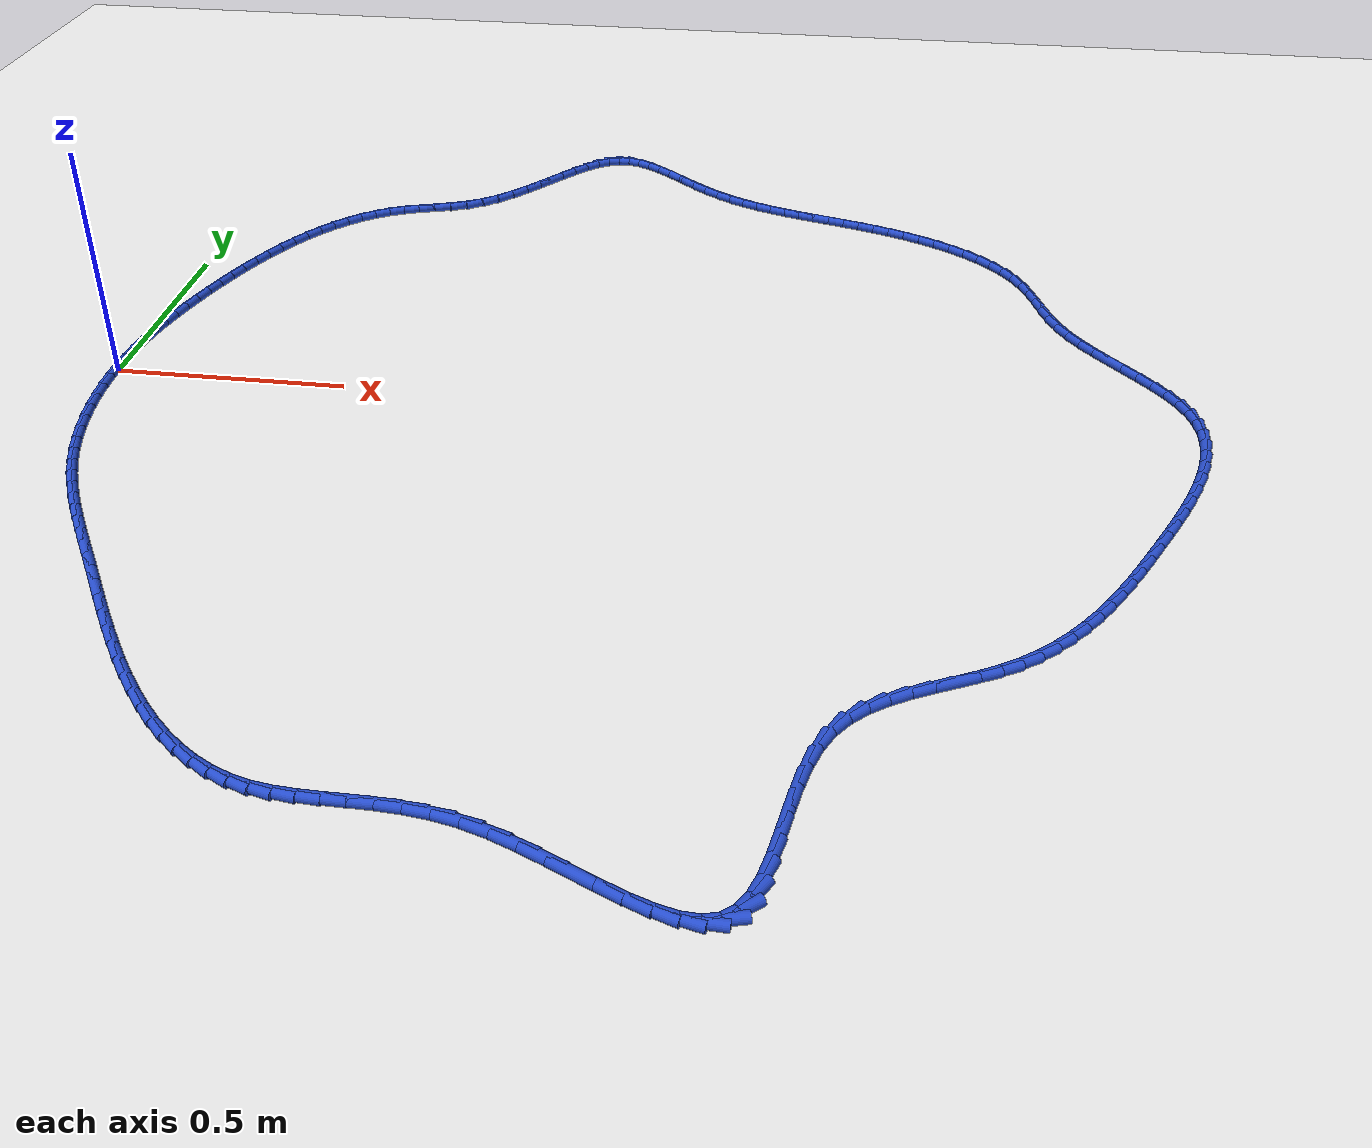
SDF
<sdf version="1.6">
 <world name="default">
  <light name="sun" type="directional">
   <pose>0 0 10 0 -0 0</pose>
   <diffuse>0.8 0.8 0.8 1</diffuse>
   <specular>0.2 0.2 0.2 1</specular>
   <attenuation>
    <range>1000</range>
    <constant>0.9</constant>
    <linear>0.01</linear>
    <quadratic>0.001</quadratic>
   </attenuation>
   <direction>-0.5 0.1 -0.9</direction>
  </light>
  <model name="ground_plane">
   <static>1</static>
   <link name="link">
    <collision name="collision">
     <geometry><plane><normal>0 0 1</normal><size>100 100</size></plane></geometry>
     <surface><friction><ode><mu>100</mu><mu2>50</mu2></ode></friction></surface>
    </collision>
    <visual name="visual">
     <cast_shadows>0</cast_shadows>
     <geometry><plane><normal>0 0 1</normal><size>100 100</size></plane></geometry>
     <material>
      <script><uri>file://media/materials/scripts/gazebo.material</uri><name>Gazebo/WhiteGlow</name></script>
     </material>
    </visual>
   </link>
  </model>
  <gravity>0 0 -9.8</gravity>
  <magnetic_field>6e-06 2.3e-05 -4.2e-05</magnetic_field>
  <atmosphere type="adiabatic"/>
  <physics name="default_physics" default="0" type="ode">
   <max_step_size>0.001</max_step_size>
   <real_time_factor>1</real_time_factor>
   <real_time_update_rate>1000</real_time_update_rate>
  </physics>
  <scene><ambient>0.4 0.4 0.4 1</ambient><background>0.7 0.7 0.7 1</background><shadows>1</shadows></scene>
  <spherical_coordinates>
   <surface_model>EARTH_WGS84</surface_model>
   <latitude_deg>0</latitude_deg>
   <longitude_deg>0</longitude_deg>
   <elevation>0</elevation>
   <heading_deg>0</heading_deg>
  </spherical_coordinates>
  <model name="line">
   <link name="link_0">
    <pose>3.469446951953614e-18 -4.163336342344337e-17 0.01 0 1.57 1.5344979702878982</pose>
    <collision name="collision">
     <geometry><cylinder><radius>0.01</radius><length>0.08</length></cylinder></geometry>
    </collision>
    <visual name="visual">
     <material>
      <script><name>Gazebo/Blue</name><uri>file://media/materials/scripts/gazebo.material</uri></script>
     </material>
     <geometry><cylinder><radius>0.01</radius><length>0.08</length></cylinder></geometry>
    </visual>
   </link>
   <link name="link_1">
    <pose>0.001436487028958093 0.03955705493695735 0.01 0 1.57 1.4928967882833355</pose>
    <collision name="collision">
     <geometry><cylinder><radius>0.01</radius><length>0.08</length></cylinder></geometry>
    </collision>
    <visual name="visual">
     <material>
      <script><name>Gazebo/Blue</name><uri>file://media/materials/scripts/gazebo.material</uri></script>
     </material>
     <geometry><cylinder><radius>0.01</radius><length>0.08</length></cylinder></geometry>
    </visual>
   </link>
   <link name="link_2">
    <pose>0.004500429375133962 0.07880943327557499 0.01 0 1.57 1.4535230239657189</pose>
    <collision name="collision">
     <geometry><cylinder><radius>0.01</radius><length>0.08</length></cylinder></geometry>
    </collision>
    <visual name="visual">
     <material>
      <script><name>Gazebo/Blue</name><uri>file://media/materials/scripts/gazebo.material</uri></script>
     </material>
     <geometry><cylinder><radius>0.01</radius><length>0.08</length></cylinder></geometry>
    </visual>
   </link>
   <link name="link_3">
    <pose>0.00910140999084232 0.11786238624754719 0.01 0 1.57 1.4167946636751974</pose>
    <collision name="collision">
     <geometry><cylinder><radius>0.01</radius><length>0.08</length></cylinder></geometry>
    </collision>
    <visual name="visual">
     <material>
      <script><name>Gazebo/Blue</name><uri>file://media/materials/scripts/gazebo.material</uri></script>
     </material>
     <geometry><cylinder><radius>0.01</radius><length>0.08</length></cylinder></geometry>
    </visual>
   </link>
   <link name="link_4">
    <pose>0.015149011828397878 0.15682116508456825 0.01 0 1.57 1.3830459368744668</pose>
    <collision name="collision">
     <geometry><cylinder><radius>0.01</radius><length>0.08</length></cylinder></geometry>
    </collision>
    <visual name="visual">
     <material>
      <script><name>Gazebo/Blue</name><uri>file://media/materials/scripts/gazebo.material</uri></script>
     </material>
     <geometry><cylinder><radius>0.01</radius><length>0.08</length></cylinder></geometry>
    </visual>
   </link>
   <link name="link_5">
    <pose>0.02255281784011534 0.19579102101833246 0.01 0 1.57 1.352523003787821</pose>
    <collision name="collision">
     <geometry><cylinder><radius>0.01</radius><length>0.08</length></cylinder></geometry>
    </collision>
    <visual name="visual">
     <material>
      <script><name>Gazebo/Blue</name><uri>file://media/materials/scripts/gazebo.material</uri></script>
     </material>
     <geometry><cylinder><radius>0.01</radius><length>0.08</length></cylinder></geometry>
    </visual>
   </link>
   <link name="link_6">
    <pose>0.031222410978309398 0.23487720528053405 0.01 0 1.57 1.3253861891705012</pose>
    <collision name="collision">
     <geometry><cylinder><radius>0.01</radius><length>0.08</length></cylinder></geometry>
    </collision>
    <visual name="visual">
     <material>
      <script><name>Gazebo/Blue</name><uri>file://media/materials/scripts/gazebo.material</uri></script>
     </material>
     <geometry><cylinder><radius>0.01</radius><length>0.08</length></cylinder></geometry>
    </visual>
   </link>
   <link name="link_7">
    <pose>0.041067374195294784 0.27418496910286744 0.01 0 1.57 1.301717111790584</pose>
    <collision name="collision">
     <geometry><cylinder><radius>0.01</radius><length>0.08</length></cylinder></geometry>
    </collision>
    <visual name="visual">
     <material>
      <script><name>Gazebo/Blue</name><uri>file://media/materials/scripts/gazebo.material</uri></script>
     </material>
     <geometry><cylinder><radius>0.01</radius><length>0.08</length></cylinder></geometry>
    </visual>
   </link>
   <link name="link_8">
    <pose>0.0519972904433862 0.31381956371702685 0.01 0 1.57 1.2815008445824343</pose>
    <collision name="collision">
     <geometry><cylinder><radius>0.01</radius><length>0.08</length></cylinder></geometry>
    </collision>
    <visual name="visual">
     <material>
      <script><name>Gazebo/Blue</name><uri>file://media/materials/scripts/gazebo.material</uri></script>
     </material>
     <geometry><cylinder><radius>0.01</radius><length>0.08</length></cylinder></geometry>
    </visual>
   </link>
   <link name="link_9">
    <pose>0.06392246939135944 0.3538845780919829 0.01 0 1.57 1.2624254854172274</pose>
    <collision name="collision">
     <geometry><cylinder><radius>0.01</radius><length>0.08</length></cylinder></geometry>
    </collision>
    <visual name="visual">
     <material>
      <script><name>Gazebo/Blue</name><uri>file://media/materials/scripts/gazebo.material</uri></script>
     </material>
     <geometry><cylinder><radius>0.01</radius><length>0.08</length></cylinder></geometry>
    </visual>
   </link>
   <link name="link_10">
    <pose>0.07681184704010782 0.3943495016245623 0.01 0 1.57 1.2404559901151915</pose>
    <collision name="collision">
     <geometry><cylinder><radius>0.01</radius><length>0.08</length></cylinder></geometry>
    </collision>
    <visual name="visual">
     <material>
      <script><name>Gazebo/Blue</name><uri>file://media/materials/scripts/gazebo.material</uri></script>
     </material>
     <geometry><cylinder><radius>0.01</radius><length>0.08</length></cylinder></geometry>
    </visual>
   </link>
   <link name="link_11">
    <pose>0.09073511784532025 0.43495335277489927 0.01 0 1.57 1.2149619485585201</pose>
    <collision name="collision">
     <geometry><cylinder><radius>0.01</radius><length>0.08</length></cylinder></geometry>
    </collision>
    <visual name="visual">
     <material>
      <script><name>Gazebo/Blue</name><uri>file://media/materials/scripts/gazebo.material</uri></script>
     </material>
     <geometry><cylinder><radius>0.01</radius><length>0.08</length></cylinder></geometry>
    </visual>
   </link>
   <link name="link_12">
    <pose>0.10577191207135259 0.4754124232241697 0.01 0 1.57 1.185610204041894</pose>
    <collision name="collision">
     <geometry><cylinder><radius>0.01</radius><length>0.08</length></cylinder></geometry>
    </collision>
    <visual name="visual">
     <material>
      <script><name>Gazebo/Blue</name><uri>file://media/materials/scripts/gazebo.material</uri></script>
     </material>
     <geometry><cylinder><radius>0.01</radius><length>0.08</length></cylinder></geometry>
    </visual>
   </link>
   <link name="link_13">
    <pose>0.12200185998256091 0.5154430046535502 0.01 0 1.57 1.1519797246476149</pose>
    <collision name="collision">
     <geometry><cylinder><radius>0.01</radius><length>0.08</length></cylinder></geometry>
    </collision>
    <visual name="visual">
     <material>
      <script><name>Gazebo/Blue</name><uri>file://media/materials/scripts/gazebo.material</uri></script>
     </material>
     <geometry><cylinder><radius>0.01</radius><length>0.08</length></cylinder></geometry>
    </visual>
   </link>
   <link name="link_14">
    <pose>0.13950459184330102 0.5547613887442162 0.01 0 1.57 1.1135589506615398</pose>
    <collision name="collision">
     <geometry><cylinder><radius>0.01</radius><length>0.08</length></cylinder></geometry>
    </collision>
    <visual name="visual">
     <material>
      <script><name>Gazebo/Blue</name><uri>file://media/materials/scripts/gazebo.material</uri></script>
     </material>
     <geometry><cylinder><radius>0.01</radius><length>0.08</length></cylinder></geometry>
    </visual>
   </link>
   <link name="link_15">
    <pose>0.15835973791792898 0.5930838671773445 0.01 0 1.57 1.069745301294318</pose>
    <collision name="collision">
     <geometry><cylinder><radius>0.01</radius><length>0.08</length></cylinder></geometry>
    </collision>
    <visual name="visual">
     <material>
      <script><name>Gazebo/Blue</name><uri>file://media/materials/scripts/gazebo.material</uri></script>
     </material>
     <geometry><cylinder><radius>0.01</radius><length>0.08</length></cylinder></geometry>
    </visual>
   </link>
   <link name="link_16">
    <pose>0.17864692847080063 0.6301267316341107 0.01 0 1.57 1.0198510211933867</pose>
    <collision name="collision">
     <geometry><cylinder><radius>0.01</radius><length>0.08</length></cylinder></geometry>
    </collision>
    <visual name="visual">
     <material>
      <script><name>Gazebo/Blue</name><uri>file://media/materials/scripts/gazebo.material</uri></script>
     </material>
     <geometry><cylinder><radius>0.01</radius><length>0.08</length></cylinder></geometry>
    </visual>
   </link>
   <link name="link_17">
    <pose>0.20044579376627192 0.665606273795691 0.01 0 1.57 0.9631217649171834</pose>
    <collision name="collision">
     <geometry><cylinder><radius>0.01</radius><length>0.08</length></cylinder></geometry>
    </collision>
    <visual name="visual">
     <material>
      <script><name>Gazebo/Blue</name><uri>file://media/materials/scripts/gazebo.material</uri></script>
     </material>
     <geometry><cylinder><radius>0.01</radius><length>0.08</length></cylinder></geometry>
    </visual>
   </link>
   <link name="link_18">
    <pose>0.22383596406869888 0.6992387853432618 0.01 0 1.57 0.8987772154755563</pose>
    <collision name="collision">
     <geometry><cylinder><radius>0.01</radius><length>0.08</length></cylinder></geometry>
    </collision>
    <visual name="visual">
     <material>
      <script><name>Gazebo/Blue</name><uri>file://media/materials/scripts/gazebo.material</uri></script>
     </material>
     <geometry><cylinder><radius>0.01</radius><length>0.08</length></cylinder></geometry>
    </visual>
   </link>
   <link name="link_19">
    <pose>0.24889706964243735 0.730740557957999 0.01 0 1.57 0.8260858051924862</pose>
    <collision name="collision">
     <geometry><cylinder><radius>0.01</radius><length>0.08</length></cylinder></geometry>
    </collision>
    <visual name="visual">
     <material>
      <script><name>Gazebo/Blue</name><uri>file://media/materials/scripts/gazebo.material</uri></script>
     </material>
     <geometry><cylinder><radius>0.01</radius><length>0.08</length></cylinder></geometry>
    </visual>
   </link>
   <link name="link_20">
    <pose>0.2757087407518434 0.7598278833210785 0.01 0 1.57 0.7444859754517545</pose>
    <collision name="collision">
     <geometry><cylinder><radius>0.01</radius><length>0.08</length></cylinder></geometry>
    </collision>
    <visual name="visual">
     <material>
      <script><name>Gazebo/Blue</name><uri>file://media/materials/scripts/gazebo.material</uri></script>
     </material>
     <geometry><cylinder><radius>0.01</radius><length>0.08</length></cylinder></geometry>
    </visual>
   </link>
   <link name="link_21">
    <pose>0.30435060766127275 0.7862170531136767 0.01 0 1.57 0.6537598464128989</pose>
    <collision name="collision">
     <geometry><cylinder><radius>0.01</radius><length>0.08</length></cylinder></geometry>
    </collision>
    <visual name="visual">
     <material>
      <script><name>Gazebo/Blue</name><uri>file://media/materials/scripts/gazebo.material</uri></script>
     </material>
     <geometry><cylinder><radius>0.01</radius><length>0.08</length></cylinder></geometry>
    </visual>
   </link>
   <link name="link_22">
    <pose>0.33490230063508153 0.8096243590169693 0.01 0 1.57 0.5542455697084279</pose>
    <collision name="collision">
     <geometry><cylinder><radius>0.01</radius><length>0.08</length></cylinder></geometry>
    </collision>
    <visual name="visual">
     <material>
      <script><name>Gazebo/Blue</name><uri>file://media/materials/scripts/gazebo.material</uri></script>
     </material>
     <geometry><cylinder><radius>0.01</radius><length>0.08</length></cylinder></geometry>
    </visual>
   </link>
   <link name="link_23">
    <pose>0.36744344993762573 0.8297660927121331 0.01 0 1.57 0.44706196624562294</pose>
    <collision name="collision">
     <geometry><cylinder><radius>0.01</radius><length>0.08</length></cylinder></geometry>
    </collision>
    <visual name="visual">
     <material>
      <script><name>Gazebo/Blue</name><uri>file://media/materials/scripts/gazebo.material</uri></script>
     </material>
     <geometry><cylinder><radius>0.01</radius><length>0.08</length></cylinder></geometry>
    </visual>
   </link>
   <link name="link_24">
    <pose>0.4020533655756618 0.8463593526339972 0.01 0 1.57 0.3491214503742008</pose>
    <collision name="collision">
     <geometry><cylinder><radius>0.01</radius><length>0.08</length></cylinder></geometry>
    </collision>
    <visual name="visual">
     <material>
      <script><name>Gazebo/Blue</name><uri>file://media/materials/scripts/gazebo.material</uri></script>
     </material>
     <geometry><cylinder><radius>0.01</radius><length>0.08</length></cylinder></geometry>
    </visual>
   </link>
   <link name="link_25">
    <pose>0.43859657393973084 0.8596622937527002 0.01 0 1.57 0.30171649680288076</pose>
    <collision name="collision">
     <geometry><cylinder><radius>0.01</radius><length>0.08</length></cylinder></geometry>
    </collision>
    <visual name="visual">
     <material>
      <script><name>Gazebo/Blue</name><uri>file://media/materials/scripts/gazebo.material</uri></script>
     </material>
     <geometry><cylinder><radius>0.01</radius><length>0.08</length></cylinder></geometry>
    </visual>
   </link>
   <link name="link_26">
    <pose>0.4763505105653126 0.8714119982933936 0.01 0 1.57 0.30918621106012206</pose>
    <collision name="collision">
     <geometry><cylinder><radius>0.01</radius><length>0.08</length></cylinder></geometry>
    </collision>
    <visual name="visual">
     <material>
      <script><name>Gazebo/Blue</name><uri>file://media/materials/scripts/gazebo.material</uri></script>
     </material>
     <geometry><cylinder><radius>0.01</radius><length>0.08</length></cylinder></geometry>
    </visual>
   </link>
   <link name="link_27">
    <pose>0.5144932133208002 0.8835959388895787 0.01 0 1.57 0.3695278509890474</pose>
    <collision name="collision">
     <geometry><cylinder><radius>0.01</radius><length>0.08</length></cylinder></geometry>
    </collision>
    <visual name="visual">
     <material>
      <script><name>Gazebo/Blue</name><uri>file://media/materials/scripts/gazebo.material</uri></script>
     </material>
     <geometry><cylinder><radius>0.01</radius><length>0.08</length></cylinder></geometry>
    </visual>
   </link>
   <link name="link_28">
    <pose>0.552202720074588 0.898201588174758 0.01 0 1.57 0.48078313941678147</pose>
    <collision name="collision">
     <geometry><cylinder><radius>0.01</radius><length>0.08</length></cylinder></geometry>
    </collision>
    <visual name="visual">
     <material>
      <script><name>Gazebo/Blue</name><uri>file://media/materials/scripts/gazebo.material</uri></script>
     </material>
     <geometry><cylinder><radius>0.01</radius><length>0.08</length></cylinder></geometry>
    </visual>
   </link>
   <link name="link_29">
    <pose>0.5886570686950691 0.9172164187824331 0.01 0 1.57 0.6248913458901066</pose>
    <collision name="collision">
     <geometry><cylinder><radius>0.01</radius><length>0.08</length></cylinder></geometry>
    </collision>
    <visual name="visual">
     <material>
      <script><name>Gazebo/Blue</name><uri>file://media/materials/scripts/gazebo.material</uri></script>
     </material>
     <geometry><cylinder><radius>0.01</radius><length>0.08</length></cylinder></geometry>
    </visual>
   </link>
   <link name="link_30">
    <pose>0.6231937090115269 0.9421283619636506 0.01 0 1.57 0.7428697556811471</pose>
    <collision name="collision">
     <geometry><cylinder><radius>0.01</radius><length>0.08</length></cylinder></geometry>
    </collision>
    <visual name="visual">
     <material>
      <script><name>Gazebo/Blue</name><uri>file://media/materials/scripts/gazebo.material</uri></script>
     </material>
     <geometry><cylinder><radius>0.01</radius><length>0.08</length></cylinder></geometry>
    </visual>
   </link>
   <link name="link_31">
    <pose>0.6558779607834962 0.9721444589460397 0.01 0 1.57 0.8250778165060558</pose>
    <collision name="collision">
     <geometry><cylinder><radius>0.01</radius><length>0.08</length></cylinder></geometry>
    </collision>
    <visual name="visual">
     <material>
      <script><name>Gazebo/Blue</name><uri>file://media/materials/scripts/gazebo.material</uri></script>
     </material>
     <geometry><cylinder><radius>0.01</radius><length>0.08</length></cylinder></geometry>
    </visual>
   </link>
   <link name="link_32">
    <pose>0.6869827696152916 1.0058211241099375 0.01 0 1.57 0.8779189661779987</pose>
    <collision name="collision">
     <geometry><cylinder><radius>0.01</radius><length>0.08</length></cylinder></geometry>
    </collision>
    <visual name="visual">
     <material>
      <script><name>Gazebo/Blue</name><uri>file://media/materials/scripts/gazebo.material</uri></script>
     </material>
     <geometry><cylinder><radius>0.01</radius><length>0.08</length></cylinder></geometry>
    </visual>
   </link>
   <link name="link_33">
    <pose>0.7167810967226008 1.041714722915088 0.01 0 1.57 0.9055846487890683</pose>
    <collision name="collision">
     <geometry><cylinder><radius>0.01</radius><length>0.08</length></cylinder></geometry>
    </collision>
    <visual name="visual">
     <material>
      <script><name>Gazebo/Blue</name><uri>file://media/materials/scripts/gazebo.material</uri></script>
     </material>
     <geometry><cylinder><radius>0.01</radius><length>0.08</length></cylinder></geometry>
    </visual>
   </link>
   <link name="link_34">
    <pose>0.7455459033211121 1.0783816208212362 0.01 0 1.57 0.9096333721276356</pose>
    <collision name="collision">
     <geometry><cylinder><radius>0.01</radius><length>0.08</length></cylinder></geometry>
    </collision>
    <visual name="visual">
     <material>
      <script><name>Gazebo/Blue</name><uri>file://media/materials/scripts/gazebo.material</uri></script>
     </material>
     <geometry><cylinder><radius>0.01</radius><length>0.08</length></cylinder></geometry>
    </visual>
   </link>
   <link name="link_35">
    <pose>0.7735501506265139 1.1143781832881277 0.01 0 1.57 0.8887101630606242</pose>
    <collision name="collision">
     <geometry><cylinder><radius>0.01</radius><length>0.08</length></cylinder></geometry>
    </collision>
    <visual name="visual">
     <material>
      <script><name>Gazebo/Blue</name><uri>file://media/materials/scripts/gazebo.material</uri></script>
     </material>
     <geometry><cylinder><radius>0.01</radius><length>0.08</length></cylinder></geometry>
    </visual>
   </link>
   <link name="link_36">
    <pose>0.8010667998544939 1.1482607757755066 0.01 0 1.57 0.8378077504988122</pose>
    <collision name="collision">
     <geometry><cylinder><radius>0.01</radius><length>0.08</length></cylinder></geometry>
    </collision>
    <visual name="visual">
     <material>
      <script><name>Gazebo/Blue</name><uri>file://media/materials/scripts/gazebo.material</uri></script>
     </material>
     <geometry><cylinder><radius>0.01</radius><length>0.08</length></cylinder></geometry>
    </visual>
   </link>
   <link name="link_37">
    <pose>0.828368812220741 1.1785857637431185 0.01 0 1.57 0.7467607978600744</pose>
    <collision name="collision">
     <geometry><cylinder><radius>0.01</radius><length>0.08</length></cylinder></geometry>
    </collision>
    <visual name="visual">
     <material>
      <script><name>Gazebo/Blue</name><uri>file://media/materials/scripts/gazebo.material</uri></script>
     </material>
     <geometry><cylinder><radius>0.01</radius><length>0.08</length></cylinder></geometry>
    </visual>
   </link>
   <link name="link_38">
    <pose>0.8557291489409421 1.2039095126507078 0.01 0 1.57 0.5983751041033184</pose>
    <collision name="collision">
     <geometry><cylinder><radius>0.01</radius><length>0.08</length></cylinder></geometry>
    </collision>
    <visual name="visual">
     <material>
      <script><name>Gazebo/Blue</name><uri>file://media/materials/scripts/gazebo.material</uri></script>
     </material>
     <geometry><cylinder><radius>0.01</radius><length>0.08</length></cylinder></geometry>
    </visual>
   </link>
   <link name="link_39">
    <pose>0.8834207712307868 1.2227883879580201 0.01 0 1.57 0.3704742805654535</pose>
    <collision name="collision">
     <geometry><cylinder><radius>0.01</radius><length>0.08</length></cylinder></geometry>
    </collision>
    <visual name="visual">
     <material>
      <script><name>Gazebo/Blue</name><uri>file://media/materials/scripts/gazebo.material</uri></script>
     </material>
     <geometry><cylinder><radius>0.01</radius><length>0.08</length></cylinder></geometry>
    </visual>
   </link>
   <link name="link_40">
    <pose>0.9117166403059624 1.2337787551247994 0.01 0 1.57 0.05695463170508301</pose>
    <collision name="collision">
     <geometry><cylinder><radius>0.01</radius><length>0.08</length></cylinder></geometry>
    </collision>
    <visual name="visual">
     <material>
      <script><name>Gazebo/Blue</name><uri>file://media/materials/scripts/gazebo.material</uri></script>
     </material>
     <geometry><cylinder><radius>0.01</radius><length>0.08</length></cylinder></geometry>
    </visual>
   </link>
   <link name="link_41">
    <pose>0.9408891647191737 1.2354420643952602 0.01 0 1.57 -0.2631267639490218</pose>
    <collision name="collision">
     <geometry><cylinder><radius>0.01</radius><length>0.08</length></cylinder></geometry>
    </collision>
    <visual name="visual">
     <material>
      <script><name>Gazebo/Blue</name><uri>file://media/materials/scripts/gazebo.material</uri></script>
     </material>
     <geometry><cylinder><radius>0.01</radius><length>0.08</length></cylinder></geometry>
    </visual>
   </link>
   <link name="link_42">
    <pose>0.9711061191557814 1.2273024515553956 0.01 0 1.57 -0.4820320225163663</pose>
    <collision name="collision">
     <geometry><cylinder><radius>0.01</radius><length>0.08</length></cylinder></geometry>
    </collision>
    <visual name="visual">
     <material>
      <script><name>Gazebo/Blue</name><uri>file://media/materials/scripts/gazebo.material</uri></script>
     </material>
     <geometry><cylinder><radius>0.01</radius><length>0.08</length></cylinder></geometry>
    </visual>
   </link>
   <link name="link_43">
    <pose>1.0023076990749809 1.2109778986400173 0.01 0 1.57 -0.6138314572361705</pose>
    <collision name="collision">
     <geometry><cylinder><radius>0.01</radius><length>0.08</length></cylinder></geometry>
    </collision>
    <visual name="visual">
     <material>
      <script><name>Gazebo/Blue</name><uri>file://media/materials/scripts/gazebo.material</uri></script>
     </material>
     <geometry><cylinder><radius>0.01</radius><length>0.08</length></cylinder></geometry>
    </visual>
   </link>
   <link name="link_44">
    <pose>1.034404197055458 1.1883615096062574 0.01 0 1.57 -0.6874664682125644</pose>
    <collision name="collision">
     <geometry><cylinder><radius>0.01</radius><length>0.08</length></cylinder></geometry>
    </collision>
    <visual name="visual">
     <material>
      <script><name>Gazebo/Blue</name><uri>file://media/materials/scripts/gazebo.material</uri></script>
     </material>
     <geometry><cylinder><radius>0.01</radius><length>0.08</length></cylinder></geometry>
    </visual>
   </link>
   <link name="link_45">
    <pose>1.067305905675899 1.161346388411249 0.01 0 1.57 -0.720607841837003</pose>
    <collision name="collision">
     <geometry><cylinder><radius>0.01</radius><length>0.08</length></cylinder></geometry>
    </collision>
    <visual name="visual">
     <material>
      <script><name>Gazebo/Blue</name><uri>file://media/materials/scripts/gazebo.material</uri></script>
     </material>
     <geometry><cylinder><radius>0.01</radius><length>0.08</length></cylinder></geometry>
    </visual>
   </link>
   <link name="link_46">
    <pose>1.1009231175149905 1.1318256390121242 0.01 0 1.57 -0.7216454191460531</pose>
    <collision name="collision">
     <geometry><cylinder><radius>0.01</radius><length>0.08</length></cylinder></geometry>
    </collision>
    <visual name="visual">
     <material>
      <script><name>Gazebo/Blue</name><uri>file://media/materials/scripts/gazebo.material</uri></script>
     </material>
     <geometry><cylinder><radius>0.01</radius><length>0.08</length></cylinder></geometry>
    </visual>
   </link>
   <link name="link_47">
    <pose>1.135166125151419 1.1016923653660164 0.01 0 1.57 -0.6925301969337198</pose>
    <collision name="collision">
     <geometry><cylinder><radius>0.01</radius><length>0.08</length></cylinder></geometry>
    </collision>
    <visual name="visual">
     <material>
      <script><name>Gazebo/Blue</name><uri>file://media/materials/scripts/gazebo.material</uri></script>
     </material>
     <geometry><cylinder><radius>0.01</radius><length>0.08</length></cylinder></geometry>
    </visual>
   </link>
   <link name="link_48">
    <pose>1.1699452211638692 1.0728396714300574 0.01 0 1.57 -0.632211776984574</pose>
    <collision name="collision">
     <geometry><cylinder><radius>0.01</radius><length>0.08</length></cylinder></geometry>
    </collision>
    <visual name="visual">
     <material>
      <script><name>Gazebo/Blue</name><uri>file://media/materials/scripts/gazebo.material</uri></script>
     </material>
     <geometry><cylinder><radius>0.01</radius><length>0.08</length></cylinder></geometry>
    </visual>
   </link>
   <link name="link_49">
    <pose>1.2051741840909804 1.047034181916328 0.01 0 1.57 -0.5604166884995994</pose>
    <collision name="collision">
     <geometry><cylinder><radius>0.01</radius><length>0.08</length></cylinder></geometry>
    </collision>
    <visual name="visual">
     <material>
      <script><name>Gazebo/Blue</name><uri>file://media/materials/scripts/gazebo.material</uri></script>
     </material>
     <geometry><cylinder><radius>0.01</radius><length>0.08</length></cylinder></geometry>
    </visual>
   </link>
   <link name="link_50">
    <pose>1.2408044807922554 1.0246750960825213 0.01 0 1.57 -0.4931067878614294</pose>
    <collision name="collision">
     <geometry><cylinder><radius>0.01</radius><length>0.08</length></cylinder></geometry>
    </collision>
    <visual name="visual">
     <material>
      <script><name>Gazebo/Blue</name><uri>file://media/materials/scripts/gazebo.material</uri></script>
     </material>
     <geometry><cylinder><radius>0.01</radius><length>0.08</length></cylinder></geometry>
    </visual>
   </link>
   <link name="link_51">
    <pose>1.2768106109563269 1.0053259252035789 0.01 0 1.57 -0.4325815828369847</pose>
    <collision name="collision">
     <geometry><cylinder><radius>0.01</radius><length>0.08</length></cylinder></geometry>
    </collision>
    <visual name="visual">
     <material>
      <script><name>Gazebo/Blue</name><uri>file://media/materials/scripts/gazebo.material</uri></script>
     </material>
     <geometry><cylinder><radius>0.01</radius><length>0.08</length></cylinder></geometry>
    </visual>
   </link>
   <link name="link_52">
    <pose>1.3131674044491928 0.9885382009033757 0.01 0 1.57 -0.38054941655955254</pose>
    <collision name="collision">
     <geometry><cylinder><radius>0.01</radius><length>0.08</length></cylinder></geometry>
    </collision>
    <visual name="visual">
     <material>
      <script><name>Gazebo/Blue</name><uri>file://media/materials/scripts/gazebo.material</uri></script>
     </material>
     <geometry><cylinder><radius>0.01</radius><length>0.08</length></cylinder></geometry>
    </visual>
   </link>
   <link name="link_53">
    <pose>1.3498496911368496 0.9738634548057874 0.01 0 1.57 -0.33827156667805686</pose>
    <collision name="collision">
     <geometry><cylinder><radius>0.01</radius><length>0.08</length></cylinder></geometry>
    </collision>
    <visual name="visual">
     <material>
      <script><name>Gazebo/Blue</name><uri>file://media/materials/scripts/gazebo.material</uri></script>
     </material>
     <geometry><cylinder><radius>0.01</radius><length>0.08</length></cylinder></geometry>
    </visual>
   </link>
   <link name="link_54">
    <pose>1.3868323008852965 0.9608532185346893 0.01 0 1.57 -0.30657638199899073</pose>
    <collision name="collision">
     <geometry><cylinder><radius>0.01</radius><length>0.08</length></cylinder></geometry>
    </collision>
    <visual name="visual">
     <material>
      <script><name>Gazebo/Blue</name><uri>file://media/materials/scripts/gazebo.material</uri></script>
     </material>
     <geometry><cylinder><radius>0.01</radius><length>0.08</length></cylinder></geometry>
    </visual>
   </link>
   <link name="link_55">
    <pose>1.4240900635605307 0.9490590237139565 0.01 0 1.57 -0.2859270738921094</pose>
    <collision name="collision">
     <geometry><cylinder><radius>0.01</radius><length>0.08</length></cylinder></geometry>
    </collision>
    <visual name="visual">
     <material>
      <script><name>Gazebo/Blue</name><uri>file://media/materials/scripts/gazebo.material</uri></script>
     </material>
     <geometry><cylinder><radius>0.01</radius><length>0.08</length></cylinder></geometry>
    </visual>
   </link>
   <link name="link_56">
    <pose>1.4615978090285489 0.9380324019674643 0.01 0 1.57 -0.27650484536732267</pose>
    <collision name="collision">
     <geometry><cylinder><radius>0.01</radius><length>0.08</length></cylinder></geometry>
    </collision>
    <visual name="visual">
     <material>
      <script><name>Gazebo/Blue</name><uri>file://media/materials/scripts/gazebo.material</uri></script>
     </material>
     <geometry><cylinder><radius>0.01</radius><length>0.08</length></cylinder></geometry>
    </visual>
   </link>
   <link name="link_57">
    <pose>1.4993303671553493 0.9273248849190877 0.01 0 1.57 -0.27827794508948317</pose>
    <collision name="collision">
     <geometry><cylinder><radius>0.01</radius><length>0.08</length></cylinder></geometry>
    </collision>
    <visual name="visual">
     <material>
      <script><name>Gazebo/Blue</name><uri>file://media/materials/scripts/gazebo.material</uri></script>
     </material>
     <geometry><cylinder><radius>0.01</radius><length>0.08</length></cylinder></geometry>
    </visual>
   </link>
   <link name="link_58">
    <pose>1.53726256780693 0.9164880041927018 0.01 0 1.57 -0.29104050074492127</pose>
    <collision name="collision">
     <geometry><cylinder><radius>0.01</radius><length>0.08</length></cylinder></geometry>
    </collision>
    <visual name="visual">
     <material>
      <script><name>Gazebo/Blue</name><uri>file://media/materials/scripts/gazebo.material</uri></script>
     </material>
     <geometry><cylinder><radius>0.01</radius><length>0.08</length></cylinder></geometry>
    </visual>
   </link>
   <link name="link_59">
    <pose>1.5753692408492876 0.9050732914121824 0.01 0 1.57 -0.3144168013787371</pose>
    <collision name="collision">
     <geometry><cylinder><radius>0.01</radius><length>0.08</length></cylinder></geometry>
    </collision>
    <visual name="visual">
     <material>
      <script><name>Gazebo/Blue</name><uri>file://media/materials/scripts/gazebo.material</uri></script>
     </material>
     <geometry><cylinder><radius>0.01</radius><length>0.08</length></cylinder></geometry>
    </visual>
   </link>
   <link name="link_60">
    <pose>1.6136252161484208 0.8926322782014043 0.01 0 1.57 -0.34783279336843115</pose>
    <collision name="collision">
     <geometry><cylinder><radius>0.01</radius><length>0.08</length></cylinder></geometry>
    </collision>
    <visual name="visual">
     <material>
      <script><name>Gazebo/Blue</name><uri>file://media/materials/scripts/gazebo.material</uri></script>
     </material>
     <geometry><cylinder><radius>0.01</radius><length>0.08</length></cylinder></geometry>
    </visual>
   </link>
   <link name="link_61">
    <pose>1.652005066051896 0.8787167250572064 0.01 0 1.57 -0.3892854697288861</pose>
    <collision name="collision">
     <geometry><cylinder><radius>0.01</radius><length>0.08</length></cylinder></geometry>
    </collision>
    <visual name="visual">
     <material>
      <script><name>Gazebo/Blue</name><uri>file://media/materials/scripts/gazebo.material</uri></script>
     </material>
     <geometry><cylinder><radius>0.01</radius><length>0.08</length></cylinder></geometry>
    </visual>
   </link>
   <link name="link_62">
    <pose>1.6903710020794993 0.8629782546714759 0.01 0 1.57 -0.4356523402527048</pose>
    <collision name="collision">
     <geometry><cylinder><radius>0.01</radius><length>0.08</length></cylinder></geometry>
    </collision>
    <visual name="visual">
     <material>
      <script><name>Gazebo/Blue</name><uri>file://media/materials/scripts/gazebo.material</uri></script>
     </material>
     <geometry><cylinder><radius>0.01</radius><length>0.08</length></cylinder></geometry>
    </visual>
   </link>
   <link name="link_63">
    <pose>1.7282974854426936 0.8453242316879979 0.01 0 1.57 -0.4874287644072484</pose>
    <collision name="collision">
     <geometry><cylinder><radius>0.01</radius><length>0.08</length></cylinder></geometry>
    </collision>
    <visual name="visual">
     <material>
      <script><name>Gazebo/Blue</name><uri>file://media/materials/scripts/gazebo.material</uri></script>
     </material>
     <geometry><cylinder><radius>0.01</radius><length>0.08</length></cylinder></geometry>
    </visual>
   </link>
   <link name="link_64">
    <pose>1.765313564805129 0.8257023817624609 0.01 0 1.57 -0.5457900237490081</pose>
    <collision name="collision">
     <geometry><cylinder><radius>0.01</radius><length>0.08</length></cylinder></geometry>
    </collision>
    <visual name="visual">
     <material>
      <script><name>Gazebo/Blue</name><uri>file://media/materials/scripts/gazebo.material</uri></script>
     </material>
     <geometry><cylinder><radius>0.01</radius><length>0.08</length></cylinder></geometry>
    </visual>
   </link>
   <link name="link_65">
    <pose>1.800948288830455 0.8040604305505514 0.01 0 1.57 -0.6120485412495208</pose>
    <collision name="collision">
     <geometry><cylinder><radius>0.01</radius><length>0.08</length></cylinder></geometry>
    </collision>
    <visual name="visual">
     <material>
      <script><name>Gazebo/Blue</name><uri>file://media/materials/scripts/gazebo.material</uri></script>
     </material>
     <geometry><cylinder><radius>0.01</radius><length>0.08</length></cylinder></geometry>
    </visual>
   </link>
   <link name="link_66">
    <pose>1.834730706182324 0.7803461037079577 0.01 0 1.57 -0.6876242683851528</pose>
    <collision name="collision">
     <geometry><cylinder><radius>0.01</radius><length>0.08</length></cylinder></geometry>
    </collision>
    <visual name="visual">
     <material>
      <script><name>Gazebo/Blue</name><uri>file://media/materials/scripts/gazebo.material</uri></script>
     </material>
     <geometry><cylinder><radius>0.01</radius><length>0.08</length></cylinder></geometry>
    </visual>
   </link>
   <link name="link_67">
    <pose>1.8661898655243836 0.7545071268903666 0.01 0 1.57 -0.7739477267924381</pose>
    <collision name="collision">
     <geometry><cylinder><radius>0.01</radius><length>0.08</length></cylinder></geometry>
    </collision>
    <visual name="visual">
     <material>
      <script><name>Gazebo/Blue</name><uri>file://media/materials/scripts/gazebo.material</uri></script>
     </material>
     <geometry><cylinder><radius>0.01</radius><length>0.08</length></cylinder></geometry>
    </visual>
   </link>
   <link name="link_68">
    <pose>1.8948548155202856 0.7264912257534659 0.01 0 1.57 -0.8722546565903321</pose>
    <collision name="collision">
     <geometry><cylinder><radius>0.01</radius><length>0.08</length></cylinder></geometry>
    </collision>
    <visual name="visual">
     <material>
      <script><name>Gazebo/Blue</name><uri>file://media/materials/scripts/gazebo.material</uri></script>
     </material>
     <geometry><cylinder><radius>0.01</radius><length>0.08</length></cylinder></geometry>
    </visual>
   </link>
   <link name="link_69">
    <pose>1.9202546048336795 0.6962461259529424 0.01 0 1.57 -0.9832345366710735</pose>
    <collision name="collision">
     <geometry><cylinder><radius>0.01</radius><length>0.08</length></cylinder></geometry>
    </collision>
    <visual name="visual">
     <material>
      <script><name>Gazebo/Blue</name><uri>file://media/materials/scripts/gazebo.material</uri></script>
     </material>
     <geometry><cylinder><radius>0.01</radius><length>0.08</length></cylinder></geometry>
    </visual>
   </link>
   <link name="link_70">
    <pose>1.9419182821282153 0.6637195531444845 0.01 0 1.57 -1.1047435366977185</pose>
    <collision name="collision">
     <geometry><cylinder><radius>0.01</radius><length>0.08</length></cylinder></geometry>
    </collision>
    <visual name="visual">
     <material>
      <script><name>Gazebo/Blue</name><uri>file://media/materials/scripts/gazebo.material</uri></script>
     </material>
     <geometry><cylinder><radius>0.01</radius><length>0.08</length></cylinder></geometry>
    </visual>
   </link>
   <link name="link_71">
    <pose>1.9594406856879956 0.6288844603962578 0.01 0 1.57 -1.2064260869912289</pose>
    <collision name="collision">
     <geometry><cylinder><radius>0.01</radius><length>0.08</length></cylinder></geometry>
    </collision>
    <visual name="visual">
     <material>
      <script><name>Gazebo/Blue</name><uri>file://media/materials/scripts/gazebo.material</uri></script>
     </material>
     <geometry><cylinder><radius>0.01</radius><length>0.08</length></cylinder></geometry>
    </visual>
   </link>
   <link name="link_72">
    <pose>1.973464366242756 0.5921155522053666 0.01 0 1.57 -1.2647775251027833</pose>
    <collision name="collision">
     <geometry><cylinder><radius>0.01</radius><length>0.08</length></cylinder></geometry>
    </collision>
    <visual name="visual">
     <material>
      <script><name>Gazebo/Blue</name><uri>file://media/materials/scripts/gazebo.material</uri></script>
     </material>
     <geometry><cylinder><radius>0.01</radius><length>0.08</length></cylinder></geometry>
    </visual>
   </link>
   <link name="link_73">
    <pose>1.9854720607530552 0.5541097073641721 0.01 0 1.57 -1.28083896134114</pose>
    <collision name="collision">
     <geometry><cylinder><radius>0.01</radius><length>0.08</length></cylinder></geometry>
    </collision>
    <visual name="visual">
     <material>
      <script><name>Gazebo/Blue</name><uri>file://media/materials/scripts/gazebo.material</uri></script>
     </material>
     <geometry><cylinder><radius>0.01</radius><length>0.08</length></cylinder></geometry>
    </visual>
   </link>
   <link name="link_74">
    <pose>1.996970155548379 0.5155728731530541 0.01 0 1.57 -1.255921573763036</pose>
    <collision name="collision">
     <geometry><cylinder><radius>0.01</radius><length>0.08</length></cylinder></geometry>
    </collision>
    <visual name="visual">
     <material>
      <script><name>Gazebo/Blue</name><uri>file://media/materials/scripts/gazebo.material</uri></script>
     </material>
     <geometry><cylinder><radius>0.01</radius><length>0.08</length></cylinder></geometry>
    </visual>
   </link>
   <link name="link_75">
    <pose>2.009465036958212 0.47721099685239343 0.01 0 1.57 -1.1901596395460023</pose>
    <collision name="collision">
     <geometry><cylinder><radius>0.01</radius><length>0.08</length></cylinder></geometry>
    </collision>
    <visual name="visual">
     <material>
      <script><name>Gazebo/Blue</name><uri>file://media/materials/scripts/gazebo.material</uri></script>
     </material>
     <geometry><cylinder><radius>0.01</radius><length>0.08</length></cylinder></geometry>
    </visual>
   </link>
   <link name="link_76">
    <pose>2.0244630913120405 0.4397300257425696 0.01 0 1.57 -1.0890325268328094</pose>
    <collision name="collision">
     <geometry><cylinder><radius>0.01</radius><length>0.08</length></cylinder></geometry>
    </collision>
    <visual name="visual">
     <material>
      <script><name>Gazebo/Blue</name><uri>file://media/materials/scripts/gazebo.material</uri></script>
     </material>
     <geometry><cylinder><radius>0.01</radius><length>0.08</length></cylinder></geometry>
    </visual>
   </link>
   <link name="link_77">
    <pose>2.0432723561949198 0.4037558578952057 0.01 0 1.57 -0.9953839938297087</pose>
    <collision name="collision">
     <geometry><cylinder><radius>0.01</radius><length>0.08</length></cylinder></geometry>
    </collision>
    <visual name="visual">
     <material>
      <script><name>Gazebo/Blue</name><uri>file://media/materials/scripts/gazebo.material</uri></script>
     </material>
     <geometry><cylinder><radius>0.01</radius><length>0.08</length></cylinder></geometry>
    </visual>
   </link>
   <link name="link_78">
    <pose>2.0656333263838604 0.36928176543898505 0.01 0 1.57 -0.9282982456410209</pose>
    <collision name="collision">
     <geometry><cylinder><radius>0.01</radius><length>0.08</length></cylinder></geometry>
    </collision>
    <visual name="visual">
     <material>
      <script><name>Gazebo/Blue</name><uri>file://media/materials/scripts/gazebo.material</uri></script>
     </material>
     <geometry><cylinder><radius>0.01</radius><length>0.08</length></cylinder></geometry>
    </visual>
   </link>
   <link name="link_79">
    <pose>2.090542085906743 0.3360005926293049 0.01 0 1.57 -0.8861530608375257</pose>
    <collision name="collision">
     <geometry><cylinder><radius>0.01</radius><length>0.08</length></cylinder></geometry>
    </collision>
    <visual name="visual">
     <material>
      <script><name>Gazebo/Blue</name><uri>file://media/materials/scripts/gazebo.material</uri></script>
     </material>
     <geometry><cylinder><radius>0.01</radius><length>0.08</length></cylinder></geometry>
    </visual>
   </link>
   <link name="link_80">
    <pose>2.116990211699759 0.30360336475807675 0.01 0 1.57 -0.8675779567971761</pose>
    <collision name="collision">
     <geometry><cylinder><radius>0.01</radius><length>0.08</length></cylinder></geometry>
    </collision>
    <visual name="visual">
     <material>
      <script><name>Gazebo/Blue</name><uri>file://media/materials/scripts/gazebo.material</uri></script>
     </material>
     <geometry><cylinder><radius>0.01</radius><length>0.08</length></cylinder></geometry>
    </visual>
   </link>
   <link name="link_81">
    <pose>2.1439692806990953 0.27178110711721254 0.01 0 1.57 -0.8722418772306473</pose>
    <collision name="collision">
     <geometry><cylinder><radius>0.01</radius><length>0.08</length></cylinder></geometry>
    </collision>
    <visual name="visual">
     <material>
      <script><name>Gazebo/Blue</name><uri>file://media/materials/scripts/gazebo.material</uri></script>
     </material>
     <geometry><cylinder><radius>0.01</radius><length>0.08</length></cylinder></geometry>
    </visual>
   </link>
   <link name="link_82">
    <pose>2.1704708698409445 0.24022484499862362 0.01 0 1.57 -0.9011647699806342</pose>
    <collision name="collision">
     <geometry><cylinder><radius>0.01</radius><length>0.08</length></cylinder></geometry>
    </collision>
    <visual name="visual">
     <material>
      <script><name>Gazebo/Blue</name><uri>file://media/materials/scripts/gazebo.material</uri></script>
     </material>
     <geometry><cylinder><radius>0.01</radius><length>0.08</length></cylinder></geometry>
    </visual>
   </link>
   <link name="link_83">
    <pose>2.1954865560614936 0.20862560369422084 0.01 0 1.57 -0.9568110245400535</pose>
    <collision name="collision">
     <geometry><cylinder><radius>0.01</radius><length>0.08</length></cylinder></geometry>
    </collision>
    <visual name="visual">
     <material>
      <script><name>Gazebo/Blue</name><uri>file://media/materials/scripts/gazebo.material</uri></script>
     </material>
     <geometry><cylinder><radius>0.01</radius><length>0.08</length></cylinder></geometry>
    </visual>
   </link>
   <link name="link_84">
    <pose>2.2180079162969335 0.17667440849591654 0.01 0 1.57 -1.0428392000214557</pose>
    <collision name="collision">
     <geometry><cylinder><radius>0.01</radius><length>0.08</length></cylinder></geometry>
    </collision>
    <visual name="visual">
     <material>
      <script><name>Gazebo/Blue</name><uri>file://media/materials/scripts/gazebo.material</uri></script>
     </material>
     <geometry><cylinder><radius>0.01</radius><length>0.08</length></cylinder></geometry>
    </visual>
   </link>
   <link name="link_85">
    <pose>2.237026527483454 0.14406228469562143 0.01 0 1.57 -1.1630115037468067</pose>
    <collision name="collision">
     <geometry><cylinder><radius>0.01</radius><length>0.08</length></cylinder></geometry>
    </collision>
    <visual name="visual">
     <material>
      <script><name>Gazebo/Blue</name><uri>file://media/materials/scripts/gazebo.material</uri></script>
     </material>
     <geometry><cylinder><radius>0.01</radius><length>0.08</length></cylinder></geometry>
    </visual>
   </link>
   <link name="link_86">
    <pose>2.251533966557244 0.11048025758524764 0.01 0 1.57 -1.3146001437915522</pose>
    <collision name="collision">
     <geometry><cylinder><radius>0.01</radius><length>0.08</length></cylinder></geometry>
    </collision>
    <visual name="visual">
     <material>
      <script><name>Gazebo/Blue</name><uri>file://media/materials/scripts/gazebo.material</uri></script>
     </material>
     <geometry><cylinder><radius>0.01</radius><length>0.08</length></cylinder></geometry>
    </visual>
   </link>
   <link name="link_87">
    <pose>2.260654742242056 0.07566184221893897 0.01 0 1.57 -1.465261764284806</pose>
    <collision name="collision">
     <geometry><cylinder><radius>0.01</radius><length>0.08</length></cylinder></geometry>
    </collision>
    <visual name="visual">
     <material>
      <script><name>Gazebo/Blue</name><uri>file://media/materials/scripts/gazebo.material</uri></script>
     </material>
     <geometry><cylinder><radius>0.01</radius><length>0.08</length></cylinder></geometry>
    </visual>
   </link>
   <link name="link_88">
    <pose>2.264469804273726 0.03964626646745025 0.01 0 1.57 1.544047833131085</pose>
    <collision name="collision">
     <geometry><cylinder><radius>0.01</radius><length>0.08</length></cylinder></geometry>
    </collision>
    <visual name="visual">
     <material>
      <script><name>Gazebo/Blue</name><uri>file://media/materials/scripts/gazebo.material</uri></script>
     </material>
     <geometry><cylinder><radius>0.01</radius><length>0.08</length></cylinder></geometry>
    </visual>
   </link>
   <link name="link_89">
    <pose>2.263478812444157 0.002606592937779756 0.01 0 1.57 1.4319334760836238</pose>
    <collision name="collision">
     <geometry><cylinder><radius>0.01</radius><length>0.08</length></cylinder></geometry>
    </collision>
    <visual name="visual">
     <material>
      <script><name>Gazebo/Blue</name><uri>file://media/materials/scripts/gazebo.material</uri></script>
     </material>
     <geometry><cylinder><radius>0.01</radius><length>0.08</length></cylinder></geometry>
    </visual>
   </link>
   <link name="link_90">
    <pose>2.258183197110086 -0.03528354982711528 0.01 0 1.57 1.3391105871862359</pose>
    <collision name="collision">
     <geometry><cylinder><radius>0.01</radius><length>0.08</length></cylinder></geometry>
    </collision>
    <visual name="visual">
     <material>
      <script><name>Gazebo/Blue</name><uri>file://media/materials/scripts/gazebo.material</uri></script>
     </material>
     <geometry><cylinder><radius>0.01</radius><length>0.08</length></cylinder></geometry>
    </visual>
   </link>
   <link name="link_91">
    <pose>2.2490843886282503 -0.07385053328427729 0.01 0 1.57 1.2634608304370893</pose>
    <collision name="collision">
     <geometry><cylinder><radius>0.01</radius><length>0.08</length></cylinder></geometry>
    </collision>
    <visual name="visual">
     <material>
      <script><name>Gazebo/Blue</name><uri>file://media/materials/scripts/gazebo.material</uri></script>
     </material>
     <geometry><cylinder><radius>0.01</radius><length>0.08</length></cylinder></geometry>
    </visual>
   </link>
   <link name="link_92">
    <pose>2.236683817355386 -0.11292072889074947 0.01 0 1.57 1.2025805851396052</pose>
    <collision name="collision">
     <geometry><cylinder><radius>0.01</radius><length>0.08</length></cylinder></geometry>
    </collision>
    <visual name="visual">
     <material>
      <script><name>Gazebo/Blue</name><uri>file://media/materials/scripts/gazebo.material</uri></script>
     </material>
     <geometry><cylinder><radius>0.01</radius><length>0.08</length></cylinder></geometry>
    </visual>
   </link>
   <link name="link_93">
    <pose>2.22148291364823 -0.15232050810357273 0.01 0 1.57 1.154273130851175</pose>
    <collision name="collision">
     <geometry><cylinder><radius>0.01</radius><length>0.08</length></cylinder></geometry>
    </collision>
    <visual name="visual">
     <material>
      <script><name>Gazebo/Blue</name><uri>file://media/materials/scripts/gazebo.material</uri></script>
     </material>
     <geometry><cylinder><radius>0.01</radius><length>0.08</length></cylinder></geometry>
    </visual>
   </link>
   <link name="link_94">
    <pose>2.2039831078635195 -0.1918762423797902 0.01 0 1.57 1.1167394899465157</pose>
    <collision name="collision">
     <geometry><cylinder><radius>0.01</radius><length>0.08</length></cylinder></geometry>
    </collision>
    <visual name="visual">
     <material>
      <script><name>Gazebo/Blue</name><uri>file://media/materials/scripts/gazebo.material</uri></script>
     </material>
     <geometry><cylinder><radius>0.01</radius><length>0.08</length></cylinder></geometry>
    </visual>
   </link>
   <link name="link_95">
    <pose>2.184685830357991 -0.23141430317644424 0.01 0 1.57 1.0886198929013462</pose>
    <collision name="collision">
     <geometry><cylinder><radius>0.01</radius><length>0.08</length></cylinder></geometry>
    </collision>
    <visual name="visual">
     <material>
      <script><name>Gazebo/Blue</name><uri>file://media/materials/scripts/gazebo.material</uri></script>
     </material>
     <geometry><cylinder><radius>0.01</radius><length>0.08</length></cylinder></geometry>
    </visual>
   </link>
   <link name="link_96">
    <pose>2.1640925114883816 -0.27076106195057736 0.01 0 1.57 1.0689793337192945</pose>
    <collision name="collision">
     <geometry><cylinder><radius>0.01</radius><length>0.08</length></cylinder></geometry>
    </collision>
    <visual name="visual">
     <material>
      <script><name>Gazebo/Blue</name><uri>file://media/materials/scripts/gazebo.material</uri></script>
     </material>
     <geometry><cylinder><radius>0.01</radius><length>0.08</length></cylinder></geometry>
    </visual>
   </link>
   <link name="link_97">
    <pose>2.142704581611428 -0.3097428901592319 0.01 0 1.57 1.0572857335739878</pose>
    <collision name="collision">
     <geometry><cylinder><radius>0.01</radius><length>0.08</length></cylinder></geometry>
    </collision>
    <visual name="visual">
     <material>
      <script><name>Gazebo/Blue</name><uri>file://media/materials/scripts/gazebo.material</uri></script>
     </material>
     <geometry><cylinder><radius>0.01</radius><length>0.08</length></cylinder></geometry>
    </visual>
   </link>
   <link name="link_98">
    <pose>2.1210234697485584 -0.3481861593286912 0.01 0 1.57 1.0509394947301052</pose>
    <collision name="collision">
     <geometry><cylinder><radius>0.01</radius><length>0.08</length></cylinder></geometry>
    </collision>
    <visual name="visual">
     <material>
      <script><name>Gazebo/Blue</name><uri>file://media/materials/scripts/gazebo.material</uri></script>
     </material>
     <geometry><cylinder><radius>0.01</radius><length>0.08</length></cylinder></geometry>
    </visual>
   </link>
   <link name="link_99">
    <pose>2.099423492134871 -0.3859238321892789 0.01 0 1.57 1.0406819910016354</pose>
    <collision name="collision">
     <geometry><cylinder><radius>0.01</radius><length>0.08</length></cylinder></geometry>
    </collision>
    <visual name="visual">
     <material>
      <script><name>Gazebo/Blue</name><uri>file://media/materials/scripts/gazebo.material</uri></script>
     </material>
     <geometry><cylinder><radius>0.01</radius><length>0.08</length></cylinder></geometry>
    </visual>
   </link>
   <link name="link_100">
    <pose>2.0778035277094418 -0.4228135244139418 0.01 0 1.57 1.0240697668642758</pose>
    <collision name="collision">
     <geometry><cylinder><radius>0.01</radius><length>0.08</length></cylinder></geometry>
    </collision>
    <visual name="visual">
     <material>
      <script><name>Gazebo/Blue</name><uri>file://media/materials/scripts/gazebo.material</uri></script>
     </material>
     <geometry><cylinder><radius>0.01</radius><length>0.08</length></cylinder></geometry>
    </visual>
   </link>
   <link name="link_101">
    <pose>2.0559513201722615 -0.4587186143928023 0.01 0 1.57 1.000768967704535</pose>
    <collision name="collision">
     <geometry><cylinder><radius>0.01</radius><length>0.08</length></cylinder></geometry>
    </collision>
    <visual name="visual">
     <material>
      <script><name>Gazebo/Blue</name><uri>file://media/materials/scripts/gazebo.material</uri></script>
     </material>
     <geometry><cylinder><radius>0.01</radius><length>0.08</length></cylinder></geometry>
    </visual>
   </link>
   <link name="link_102">
    <pose>2.0336546132233244 -0.4935024805159829 0.01 0 1.57 0.9704494219895214</pose>
    <collision name="collision">
     <geometry><cylinder><radius>0.01</radius><length>0.08</length></cylinder></geometry>
    </collision>
    <visual name="visual">
     <material>
      <script><name>Gazebo/Blue</name><uri>file://media/materials/scripts/gazebo.material</uri></script>
     </material>
     <geometry><cylinder><radius>0.01</radius><length>0.08</length></cylinder></geometry>
    </visual>
   </link>
   <link name="link_103">
    <pose>2.0107011505626207 -0.5270285011736066 0.01 0 1.57 0.9328191478072869</pose>
    <collision name="collision">
     <geometry><cylinder><radius>0.01</radius><length>0.08</length></cylinder></geometry>
    </collision>
    <visual name="visual">
     <material>
      <script><name>Gazebo/Blue</name><uri>file://media/materials/scripts/gazebo.material</uri></script>
     </material>
     <geometry><cylinder><radius>0.01</radius><length>0.08</length></cylinder></geometry>
    </visual>
   </link>
   <link name="link_104">
    <pose>1.986878675890144 -0.5591600547557949 0.01 0 1.57 0.8876758879261578</pose>
    <collision name="collision">
     <geometry><cylinder><radius>0.01</radius><length>0.08</length></cylinder></geometry>
    </collision>
    <visual name="visual">
     <material>
      <script><name>Gazebo/Blue</name><uri>file://media/materials/scripts/gazebo.material</uri></script>
     </material>
     <geometry><cylinder><radius>0.01</radius><length>0.08</length></cylinder></geometry>
    </visual>
   </link>
   <link name="link_105">
    <pose>1.9619749329058853 -0.5897605196526706 0.01 0 1.57 0.8349763289532054</pose>
    <collision name="collision">
     <geometry><cylinder><radius>0.01</radius><length>0.08</length></cylinder></geometry>
    </collision>
    <visual name="visual">
     <material>
      <script><name>Gazebo/Blue</name><uri>file://media/materials/scripts/gazebo.material</uri></script>
     </material>
     <geometry><cylinder><radius>0.01</radius><length>0.08</length></cylinder></geometry>
    </visual>
   </link>
   <link name="link_106">
    <pose>1.9357776653098375 -0.6186932742543564 0.01 0 1.57 0.7749186930595295</pose>
    <collision name="collision">
     <geometry><cylinder><radius>0.01</radius><length>0.08</length></cylinder></geometry>
    </collision>
    <visual name="visual">
     <material>
      <script><name>Gazebo/Blue</name><uri>file://media/materials/scripts/gazebo.material</uri></script>
     </material>
     <geometry><cylinder><radius>0.01</radius><length>0.08</length></cylinder></geometry>
    </visual>
   </link>
   <link name="link_107">
    <pose>1.9080746168019924 -0.6458216969509747 0.01 0 1.57 0.708026309735153</pose>
    <collision name="collision">
     <geometry><cylinder><radius>0.01</radius><length>0.08</length></cylinder></geometry>
    </collision>
    <visual name="visual">
     <material>
      <script><name>Gazebo/Blue</name><uri>file://media/materials/scripts/gazebo.material</uri></script>
     </material>
     <geometry><cylinder><radius>0.01</radius><length>0.08</length></cylinder></geometry>
    </visual>
   </link>
   <link name="link_108">
    <pose>1.8786535310823425 -0.671009166132648 0.01 0 1.57 0.635210237496764</pose>
    <collision name="collision">
     <geometry><cylinder><radius>0.01</radius><length>0.08</length></cylinder></geometry>
    </collision>
    <visual name="visual">
     <material>
      <script><name>Gazebo/Blue</name><uri>file://media/materials/scripts/gazebo.material</uri></script>
     </material>
     <geometry><cylinder><radius>0.01</radius><length>0.08</length></cylinder></geometry>
    </visual>
   </link>
   <link name="link_109">
    <pose>1.8473021518508794 -0.6941190601894995 0.01 0 1.57 0.5577859163721824</pose>
    <collision name="collision">
     <geometry><cylinder><radius>0.01</radius><length>0.08</length></cylinder></geometry>
    </collision>
    <visual name="visual">
     <material>
      <script><name>Gazebo/Blue</name><uri>file://media/materials/scripts/gazebo.material</uri></script>
     </material>
     <geometry><cylinder><radius>0.01</radius><length>0.08</length></cylinder></geometry>
    </visual>
   </link>
   <link name="link_110">
    <pose>1.8138083100994142 -0.7150148445384512 0.01 0 1.57 0.48548808842270263</pose>
    <collision name="collision">
     <geometry><cylinder><radius>0.01</radius><length>0.08</length></cylinder></geometry>
    </collision>
    <visual name="visual">
     <material>
      <script><name>Gazebo/Blue</name><uri>file://media/materials/scripts/gazebo.material</uri></script>
     </material>
     <geometry><cylinder><radius>0.01</radius><length>0.08</length></cylinder></geometry>
    </visual>
   </link>
   <link name="link_111">
    <pose>1.778201705572507 -0.7338011190358446 0.01 0 1.57 0.4437118482079033</pose>
    <collision name="collision">
     <geometry><cylinder><radius>0.01</radius><length>0.08</length></cylinder></geometry>
    </collision>
    <visual name="visual">
     <material>
      <script><name>Gazebo/Blue</name><uri>file://media/materials/scripts/gazebo.material</uri></script>
     </material>
     <geometry><cylinder><radius>0.01</radius><length>0.08</length></cylinder></geometry>
    </visual>
   </link>
   <link name="link_112">
    <pose>1.7412818618404293 -0.751349970179242 0.01 0 1.57 0.4352647840380532</pose>
    <collision name="collision">
     <geometry><cylinder><radius>0.01</radius><length>0.08</length></cylinder></geometry>
    </collision>
    <visual name="visual">
     <material>
      <script><name>Gazebo/Blue</name><uri>file://media/materials/scripts/gazebo.material</uri></script>
     </material>
     <geometry><cylinder><radius>0.01</radius><length>0.08</length></cylinder></geometry>
    </visual>
   </link>
   <link name="link_113">
    <pose>1.7040011196790115 -0.7686858377188561 0.01 0 1.57 0.45933571590329275</pose>
    <collision name="collision">
     <geometry><cylinder><radius>0.01</radius><length>0.08</length></cylinder></geometry>
    </collision>
    <visual name="visual">
     <material>
      <script><name>Gazebo/Blue</name><uri>file://media/materials/scripts/gazebo.material</uri></script>
     </material>
     <geometry><cylinder><radius>0.01</radius><length>0.08</length></cylinder></geometry>
    </visual>
   </link>
   <link name="link_114">
    <pose>1.6673118198640846 -0.7868331614048992 0.01 0 1.57 0.5170000016254456</pose>
    <collision name="collision">
     <geometry><cylinder><radius>0.01</radius><length>0.08</length></cylinder></geometry>
    </collision>
    <visual name="visual">
     <material>
      <script><name>Gazebo/Blue</name><uri>file://media/materials/scripts/gazebo.material</uri></script>
     </material>
     <geometry><cylinder><radius>0.01</radius><length>0.08</length></cylinder></geometry>
    </visual>
   </link>
   <link name="link_115">
    <pose>1.6321663031714786 -0.8068163809875845 0.01 0 1.57 0.6104994069622448</pose>
    <collision name="collision">
     <geometry><cylinder><radius>0.01</radius><length>0.08</length></cylinder></geometry>
    </collision>
    <visual name="visual">
     <material>
      <script><name>Gazebo/Blue</name><uri>file://media/materials/scripts/gazebo.material</uri></script>
     </material>
     <geometry><cylinder><radius>0.01</radius><length>0.08</length></cylinder></geometry>
    </visual>
   </link>
   <link name="link_116">
    <pose>1.5995169103770246 -0.8296599362171234 0.01 0 1.57 0.7412175580372814</pose>
    <collision name="collision">
     <geometry><cylinder><radius>0.01</radius><length>0.08</length></cylinder></geometry>
    </collision>
    <visual name="visual">
     <material>
      <script><name>Gazebo/Blue</name><uri>file://media/materials/scripts/gazebo.material</uri></script>
     </material>
     <geometry><cylinder><radius>0.01</radius><length>0.08</length></cylinder></geometry>
    </visual>
   </link>
   <link name="link_117">
    <pose>1.5703159822565533 -0.8563882668437292 0.01 0 1.57 0.9059606023154728</pose>
    <collision name="collision">
     <geometry><cylinder><radius>0.01</radius><length>0.08</length></cylinder></geometry>
    </collision>
    <visual name="visual">
     <material>
      <script><name>Gazebo/Blue</name><uri>file://media/materials/scripts/gazebo.material</uri></script>
     </material>
     <geometry><cylinder><radius>0.01</radius><length>0.08</length></cylinder></geometry>
    </visual>
   </link>
   <link name="link_118">
    <pose>1.5455158595858949 -0.8880258126176144 0.01 0 1.57 1.08191504695779</pose>
    <collision name="collision">
     <geometry><cylinder><radius>0.01</radius><length>0.08</length></cylinder></geometry>
    </collision>
    <visual name="visual">
     <material>
      <script><name>Gazebo/Blue</name><uri>file://media/materials/scripts/gazebo.material</uri></script>
     </material>
     <geometry><cylinder><radius>0.01</radius><length>0.08</length></cylinder></geometry>
    </visual>
   </link>
   <link name="link_119">
    <pose>1.5257506949724549 -0.9251817298362242 0.01 0 1.57 1.213858199481864</pose>
    <collision name="collision">
     <geometry><cylinder><radius>0.01</radius><length>0.08</length></cylinder></geometry>
    </collision>
    <visual name="visual">
     <material>
      <script><name>Gazebo/Blue</name><uri>file://media/materials/scripts/gazebo.material</uri></script>
     </material>
     <geometry><cylinder><radius>0.01</radius><length>0.08</length></cylinder></geometry>
    </visual>
   </link>
   <link name="link_120">
    <pose>1.5102792325542291 -0.9666700597210155 0.01 0 1.57 1.299287680782205</pose>
    <collision name="collision">
     <geometry><cylinder><radius>0.01</radius><length>0.08</length></cylinder></geometry>
    </collision>
    <visual name="visual">
     <material>
      <script><name>Gazebo/Blue</name><uri>file://media/materials/scripts/gazebo.material</uri></script>
     </material>
     <geometry><cylinder><radius>0.01</radius><length>0.08</length></cylinder></geometry>
    </visual>
   </link>
   <link name="link_121">
    <pose>1.4979886637181934 -1.0108199112280705 0.01 0 1.57 1.3480931344271125</pose>
    <collision name="collision">
     <geometry><cylinder><radius>0.01</radius><length>0.08</length></cylinder></geometry>
    </collision>
    <visual name="visual">
     <material>
      <script><name>Gazebo/Blue</name><uri>file://media/materials/scripts/gazebo.material</uri></script>
     </material>
     <geometry><cylinder><radius>0.01</radius><length>0.08</length></cylinder></geometry>
    </visual>
   </link>
   <link name="link_122">
    <pose>1.4877661739085 -1.055960385557195 0.01 0 1.57 1.3652999691165337</pose>
    <collision name="collision">
     <geometry><cylinder><radius>0.01</radius><length>0.08</length></cylinder></geometry>
    </collision>
    <visual name="visual">
     <material>
      <script><name>Gazebo/Blue</name><uri>file://media/materials/scripts/gazebo.material</uri></script>
     </material>
     <geometry><cylinder><radius>0.01</radius><length>0.08</length></cylinder></geometry>
    </visual>
   </link>
   <link name="link_123">
    <pose>1.4784989485693008 -1.1004205839081942 0.01 0 1.57 1.350606806682761</pose>
    <collision name="collision">
     <geometry><cylinder><radius>0.01</radius><length>0.08</length></cylinder></geometry>
    </collision>
    <visual name="visual">
     <material>
      <script><name>Gazebo/Blue</name><uri>file://media/materials/scripts/gazebo.material</uri></script>
     </material>
     <geometry><cylinder><radius>0.01</radius><length>0.08</length></cylinder></geometry>
    </visual>
   </link>
   <link name="link_124">
    <pose>1.4690741731447483 -1.1425296074808733 0.01 0 1.57 1.2970380406903523</pose>
    <collision name="collision">
     <geometry><cylinder><radius>0.01</radius><length>0.08</length></cylinder></geometry>
    </collision>
    <visual name="visual">
     <material>
      <script><name>Gazebo/Blue</name><uri>file://media/materials/scripts/gazebo.material</uri></script>
     </material>
     <geometry><cylinder><radius>0.01</radius><length>0.08</length></cylinder></geometry>
    </visual>
   </link>
   <link name="link_125">
    <pose>1.4583790330789954 -1.1806165574750378 0.01 0 1.57 1.1870812633671495</pose>
    <collision name="collision">
     <geometry><cylinder><radius>0.01</radius><length>0.08</length></cylinder></geometry>
    </collision>
    <visual name="visual">
     <material>
      <script><name>Gazebo/Blue</name><uri>file://media/materials/scripts/gazebo.material</uri></script>
     </material>
     <geometry><cylinder><radius>0.01</radius><length>0.08</length></cylinder></geometry>
    </visual>
   </link>
   <link name="link_126">
    <pose>1.445300713816193 -1.2130105350904927 0.01 0 1.57 0.985909724917114</pose>
    <collision name="collision">
     <geometry><cylinder><radius>0.01</radius><length>0.08</length></cylinder></geometry>
    </collision>
    <visual name="visual">
     <material>
      <script><name>Gazebo/Blue</name><uri>file://media/materials/scripts/gazebo.material</uri></script>
     </material>
     <geometry><cylinder><radius>0.01</radius><length>0.08</length></cylinder></geometry>
    </visual>
   </link>
   <link name="link_127">
    <pose>1.4287264008004943 -1.238040641527042 0.01 0 1.57 0.6480998433481684</pose>
    <collision name="collision">
     <geometry><cylinder><radius>0.01</radius><length>0.08</length></cylinder></geometry>
    </collision>
    <visual name="visual">
     <material>
      <script><name>Gazebo/Blue</name><uri>file://media/materials/scripts/gazebo.material</uri></script>
     </material>
     <geometry><cylinder><radius>0.01</radius><length>0.08</length></cylinder></geometry>
    </visual>
   </link>
   <link name="link_128">
    <pose>1.4075606311939122 -1.2540675833021124 0.01 0 1.57 0.24957789033742994</pose>
    <collision name="collision">
     <geometry><cylinder><radius>0.01</radius><length>0.08</length></cylinder></geometry>
    </collision>
    <visual name="visual">
     <material>
      <script><name>Gazebo/Blue</name><uri>file://media/materials/scripts/gazebo.material</uri></script>
     </material>
     <geometry><cylinder><radius>0.01</radius><length>0.08</length></cylinder></geometry>
    </visual>
   </link>
   <link name="link_129">
    <pose>1.3814111305430588 -1.2607328906775706 0.01 0 1.57 -0.04442675570059731</pose>
    <collision name="collision">
     <geometry><cylinder><radius>0.01</radius><length>0.08</length></cylinder></geometry>
    </collision>
    <visual name="visual">
     <material>
      <script><name>Gazebo/Blue</name><uri>file://media/materials/scripts/gazebo.material</uri></script>
     </material>
     <geometry><cylinder><radius>0.01</radius><length>0.08</length></cylinder></geometry>
    </visual>
   </link>
   <link name="link_130">
    <pose>1.3508160141181613 -1.2593727539462023 0.01 0 1.57 -0.2264014122634015</pose>
    <collision name="collision">
     <geometry><cylinder><radius>0.01</radius><length>0.08</length></cylinder></geometry>
    </collision>
    <visual name="visual">
     <material>
      <script><name>Gazebo/Blue</name><uri>file://media/materials/scripts/gazebo.material</uri></script>
     </material>
     <geometry><cylinder><radius>0.01</radius><length>0.08</length></cylinder></geometry>
    </visual>
   </link>
   <link name="link_131">
    <pose>1.3163773087046546 -1.2514397751448076 0.01 0 1.57 -0.33348244298107926</pose>
    <collision name="collision">
     <geometry><cylinder><radius>0.01</radius><length>0.08</length></cylinder></geometry>
    </collision>
    <visual name="visual">
     <material>
      <script><name>Gazebo/Blue</name><uri>file://media/materials/scripts/gazebo.material</uri></script>
     </material>
     <geometry><cylinder><radius>0.01</radius><length>0.08</length></cylinder></geometry>
    </visual>
   </link>
   <link name="link_132">
    <pose>1.278697041087977 -1.2383865563101895 0.01 0 1.57 -0.3931191735830683</pose>
    <collision name="collision">
     <geometry><cylinder><radius>0.01</radius><length>0.08</length></cylinder></geometry>
    </collision>
    <visual name="visual">
     <material>
      <script><name>Gazebo/Blue</name><uri>file://media/materials/scripts/gazebo.material</uri></script>
     </material>
     <geometry><cylinder><radius>0.01</radius><length>0.08</length></cylinder></geometry>
    </visual>
   </link>
   <link name="link_133">
    <pose>1.238377238053562 -1.2216656994791477 0.01 0 1.57 -0.4203991112648313</pose>
    <collision name="collision">
     <geometry><cylinder><radius>0.01</radius><length>0.08</length></cylinder></geometry>
    </collision>
    <visual name="visual">
     <material>
      <script><name>Gazebo/Blue</name><uri>file://media/materials/scripts/gazebo.material</uri></script>
     </material>
     <geometry><cylinder><radius>0.01</radius><length>0.08</length></cylinder></geometry>
    </visual>
   </link>
   <link name="link_134">
    <pose>1.1960199263868465 -1.2027298066884842 0.01 0 1.57 -0.42269382660078836</pose>
    <collision name="collision">
     <geometry><cylinder><radius>0.01</radius><length>0.08</length></cylinder></geometry>
    </collision>
    <visual name="visual">
     <material>
      <script><name>Gazebo/Blue</name><uri>file://media/materials/scripts/gazebo.material</uri></script>
     </material>
     <geometry><cylinder><radius>0.01</radius><length>0.08</length></cylinder></geometry>
    </visual>
   </link>
   <link name="link_135">
    <pose>1.1522271328732658 -1.183031479974999 0.01 0 1.57 -0.4026675959763152</pose>
    <collision name="collision">
     <geometry><cylinder><radius>0.01</radius><length>0.08</length></cylinder></geometry>
    </collision>
    <visual name="visual">
     <material>
      <script><name>Gazebo/Blue</name><uri>file://media/materials/scripts/gazebo.material</uri></script>
     </material>
     <geometry><cylinder><radius>0.01</radius><length>0.08</length></cylinder></geometry>
    </visual>
   </link>
   <link name="link_136">
    <pose>1.1076008842982554 -1.1640233213754942 0.01 0 1.57 -0.3596256476075354</pose>
    <collision name="collision">
     <geometry><cylinder><radius>0.01</radius><length>0.08</length></cylinder></geometry>
    </collision>
    <visual name="visual">
     <material>
      <script><name>Gazebo/Blue</name><uri>file://media/materials/scripts/gazebo.material</uri></script>
     </material>
     <geometry><cylinder><radius>0.01</radius><length>0.08</length></cylinder></geometry>
    </visual>
   </link>
   <link name="link_137">
    <pose>1.062743207447251 -1.14715793292677 0.01 0 1.57 -0.2898865409477487</pose>
    <collision name="collision">
     <geometry><cylinder><radius>0.01</radius><length>0.08</length></cylinder></geometry>
    </collision>
    <visual name="visual">
     <material>
      <script><name>Gazebo/Blue</name><uri>file://media/materials/scripts/gazebo.material</uri></script>
     </material>
     <geometry><cylinder><radius>0.01</radius><length>0.08</length></cylinder></geometry>
    </visual>
   </link>
   <link name="link_138">
    <pose>1.0182561291056886 -1.133887916665628 0.01 0 1.57 -0.1953450958879274</pose>
    <collision name="collision">
     <geometry><cylinder><radius>0.01</radius><length>0.08</length></cylinder></geometry>
    </collision>
    <visual name="visual">
     <material>
      <script><name>Gazebo/Blue</name><uri>file://media/materials/scripts/gazebo.material</uri></script>
     </material>
     <geometry><cylinder><radius>0.01</radius><length>0.08</length></cylinder></geometry>
    </visual>
   </link>
   <link name="link_139">
    <pose>0.9746516291510412 -1.1252599645216852 0.01 0 1.57 -0.1092284554380349</pose>
    <collision name="collision">
     <geometry><cylinder><radius>0.01</radius><length>0.08</length></cylinder></geometry>
    </collision>
    <visual name="visual">
     <material>
      <script><name>Gazebo/Blue</name><uri>file://media/materials/scripts/gazebo.material</uri></script>
     </material>
     <geometry><cylinder><radius>0.01</radius><length>0.08</length></cylinder></geometry>
    </visual>
   </link>
   <link name="link_140">
    <pose>0.9320574862811618 -1.1205888806171205 0.01 0 1.57 -0.0447558155990737</pose>
    <collision name="collision">
     <geometry><cylinder><radius>0.01</radius><length>0.08</length></cylinder></geometry>
    </collision>
    <visual name="visual">
     <material>
      <script><name>Gazebo/Blue</name><uri>file://media/materials/scripts/gazebo.material</uri></script>
     </material>
     <geometry><cylinder><radius>0.01</radius><length>0.08</length></cylinder></geometry>
    </visual>
   </link>
   <link name="link_141">
    <pose>0.8904990306077739 -1.1187276551427148 0.01 0 1.57 -0.004898570891929254</pose>
    <collision name="collision">
     <geometry><cylinder><radius>0.01</radius><length>0.08</length></cylinder></geometry>
    </collision>
    <visual name="visual">
     <material>
      <script><name>Gazebo/Blue</name><uri>file://media/materials/scripts/gazebo.material</uri></script>
     </material>
     <geometry><cylinder><radius>0.01</radius><length>0.08</length></cylinder></geometry>
    </visual>
   </link>
   <link name="link_142">
    <pose>0.8500015912862997 -1.1185292739784698 0.01 0 1.57 0.008054639699042732</pose>
    <collision name="collision">
     <geometry><cylinder><radius>0.01</radius><length>0.08</length></cylinder></geometry>
    </collision>
    <visual name="visual">
     <material>
      <script><name>Gazebo/Blue</name><uri>file://media/materials/scripts/gazebo.material</uri></script>
     </material>
     <geometry><cylinder><radius>0.01</radius><length>0.08</length></cylinder></geometry>
    </visual>
   </link>
   <link name="link_143">
    <pose>0.8105904974721632 -1.1188467230043877 0.01 0 1.57 -0.00819145286385281</pose>
    <collision name="collision">
     <geometry><cylinder><radius>0.01</radius><length>0.08</length></cylinder></geometry>
    </collision>
    <visual name="visual">
     <material>
      <script><name>Gazebo/Blue</name><uri>file://media/materials/scripts/gazebo.material</uri></script>
     </material>
     <geometry><cylinder><radius>0.01</radius><length>0.08</length></cylinder></geometry>
    </visual>
   </link>
   <link name="link_144">
    <pose>0.7722910783207865 -1.1185329881004713 0.01 0 1.57 -0.056232285333852106</pose>
    <collision name="collision">
     <geometry><cylinder><radius>0.01</radius><length>0.08</length></cylinder></geometry>
    </collision>
    <visual name="visual">
     <material>
      <script><name>Gazebo/Blue</name><uri>file://media/materials/scripts/gazebo.material</uri></script>
     </material>
     <geometry><cylinder><radius>0.01</radius><length>0.08</length></cylinder></geometry>
    </visual>
   </link>
   <link name="link_145">
    <pose>0.7351286629875919 -1.116441055146722 0.01 0 1.57 -0.13847292085413124</pose>
    <collision name="collision">
     <geometry><cylinder><radius>0.01</radius><length>0.08</length></cylinder></geometry>
    </collision>
    <visual name="visual">
     <material>
      <script><name>Gazebo/Blue</name><uri>file://media/materials/scripts/gazebo.material</uri></script>
     </material>
     <geometry><cylinder><radius>0.01</radius><length>0.08</length></cylinder></geometry>
    </visual>
   </link>
   <link name="link_146">
    <pose>0.6991285806280024 -1.1114239100231424 0.01 0 1.57 -0.25140170360723935</pose>
    <collision name="collision">
     <geometry><cylinder><radius>0.01</radius><length>0.08</length></cylinder></geometry>
    </collision>
    <visual name="visual">
     <material>
      <script><name>Gazebo/Blue</name><uri>file://media/materials/scripts/gazebo.material</uri></script>
     </material>
     <geometry><cylinder><radius>0.01</radius><length>0.08</length></cylinder></geometry>
    </visual>
   </link>
   <link name="link_147">
    <pose>0.6643079679480322 -1.1024807387874478 0.01 0 1.57 -0.36660909459841534</pose>
    <collision name="collision">
     <geometry><cylinder><radius>0.01</radius><length>0.08</length></cylinder></geometry>
    </collision>
    <visual name="visual">
     <material>
      <script><name>Gazebo/Blue</name><uri>file://media/materials/scripts/gazebo.material</uri></script>
     </material>
     <geometry><cylinder><radius>0.01</radius><length>0.08</length></cylinder></geometry>
    </visual>
   </link>
   <link name="link_148">
    <pose>0.630631328051367 -1.0895500121521116 0.01 0 1.57 -0.4713228557261431</pose>
    <collision name="collision">
     <geometry><cylinder><radius>0.01</radius><length>0.08</length></cylinder></geometry>
    </collision>
    <visual name="visual">
     <material>
      <script><name>Gazebo/Blue</name><uri>file://media/materials/scripts/gazebo.material</uri></script>
     </material>
     <geometry><cylinder><radius>0.01</radius><length>0.08</length></cylinder></geometry>
    </visual>
   </link>
   <link name="link_149">
    <pose>0.5980423494854128 -1.0729416516223818 0.01 0 1.57 -0.5643120643564213</pose>
    <collision name="collision">
     <geometry><cylinder><radius>0.01</radius><length>0.08</length></cylinder></geometry>
    </collision>
    <visual name="visual">
     <material>
      <script><name>Gazebo/Blue</name><uri>file://media/materials/scripts/gazebo.material</uri></script>
     </material>
     <geometry><cylinder><radius>0.01</radius><length>0.08</length></cylinder></geometry>
    </visual>
   </link>
   <link name="link_150">
    <pose>0.5664846693381422 -1.0529664970342332 0.01 0 1.57 -0.6454663808427586</pose>
    <collision name="collision">
     <geometry><cylinder><radius>0.01</radius><length>0.08</length></cylinder></geometry>
    </collision>
    <visual name="visual">
     <material>
      <script><name>Gazebo/Blue</name><uri>file://media/materials/scripts/gazebo.material</uri></script>
     </material>
     <geometry><cylinder><radius>0.01</radius><length>0.08</length></cylinder></geometry>
    </visual>
   </link>
   <link name="link_151">
    <pose>0.5359019246975284 -1.0299353882236406 0.01 0 1.57 -0.7153843416996919</pose>
    <collision name="collision">
     <geometry><cylinder><radius>0.01</radius><length>0.08</length></cylinder></geometry>
    </collision>
    <visual name="visual">
     <material>
      <script><name>Gazebo/Blue</name><uri>file://media/materials/scripts/gazebo.material</uri></script>
     </material>
     <geometry><cylinder><radius>0.01</radius><length>0.08</length></cylinder></geometry>
    </visual>
   </link>
   <link name="link_152">
    <pose>0.5062377526515445 -1.0041591650265784 0.01 0 1.57 -0.7750242311550057</pose>
    <collision name="collision">
     <geometry><cylinder><radius>0.01</radius><length>0.08</length></cylinder></geometry>
    </collision>
    <visual name="visual">
     <material>
      <script><name>Gazebo/Blue</name><uri>file://media/materials/scripts/gazebo.material</uri></script>
     </material>
     <geometry><cylinder><radius>0.01</radius><length>0.08</length></cylinder></geometry>
    </visual>
   </link>
   <link name="link_153">
    <pose>0.4774357902881636 -0.9759486672790213 0.01 0 1.57 -0.8254558417189907</pose>
    <collision name="collision">
     <geometry><cylinder><radius>0.01</radius><length>0.08</length></cylinder></geometry>
    </collision>
    <visual name="visual">
     <material>
      <script><name>Gazebo/Blue</name><uri>file://media/materials/scripts/gazebo.material</uri></script>
     </material>
     <geometry><cylinder><radius>0.01</radius><length>0.08</length></cylinder></geometry>
    </visual>
   </link>
   <link name="link_154">
    <pose>0.44943967469535834 -0.9456147348169429 0.01 0 1.57 -0.8677110829742587</pose>
    <collision name="collision">
     <geometry><cylinder><radius>0.01</radius><length>0.08</length></cylinder></geometry>
    </collision>
    <visual name="visual">
     <material>
      <script><name>Gazebo/Blue</name><uri>file://media/materials/scripts/gazebo.material</uri></script>
     </material>
     <geometry><cylinder><radius>0.01</radius><length>0.08</length></cylinder></geometry>
    </visual>
   </link>
   <link name="link_155">
    <pose>0.42219304296110294 -0.9134682074763192 0.01 0 1.57 -0.9027069144915741</pose>
    <collision name="collision">
     <geometry><cylinder><radius>0.01</radius><length>0.08</length></cylinder></geometry>
    </collision>
    <visual name="visual">
     <material>
      <script><name>Gazebo/Blue</name><uri>file://media/materials/scripts/gazebo.material</uri></script>
     </material>
     <geometry><cylinder><radius>0.01</radius><length>0.08</length></cylinder></geometry>
    </visual>
   </link>
   <link name="link_156">
    <pose>0.3956395321733701 -0.879819925093124 0.01 0 1.57 -0.9312129968575945</pose>
    <collision name="collision">
     <geometry><cylinder><radius>0.01</radius><length>0.08</length></cylinder></geometry>
    </collision>
    <visual name="visual">
     <material>
      <script><name>Gazebo/Blue</name><uri>file://media/materials/scripts/gazebo.material</uri></script>
     </material>
     <geometry><cylinder><radius>0.01</radius><length>0.08</length></cylinder></geometry>
    </visual>
   </link>
   <link name="link_157">
    <pose>0.36972277942013304 -0.8449807275033328 0.01 0 1.57 -0.9538433681280016</pose>
    <collision name="collision">
     <geometry><cylinder><radius>0.01</radius><length>0.08</length></cylinder></geometry>
    </collision>
    <visual name="visual">
     <material>
      <script><name>Gazebo/Blue</name><uri>file://media/materials/scripts/gazebo.material</uri></script>
     </material>
     <geometry><cylinder><radius>0.01</radius><length>0.08</length></cylinder></geometry>
    </visual>
   </link>
   <link name="link_158">
    <pose>0.34438642178936474 -0.8092614545429191 0.01 0 1.57 -0.9710587757857049</pose>
    <collision name="collision">
     <geometry><cylinder><radius>0.01</radius><length>0.08</length></cylinder></geometry>
    </collision>
    <visual name="visual">
     <material>
      <script><name>Gazebo/Blue</name><uri>file://media/materials/scripts/gazebo.material</uri></script>
     </material>
     <geometry><cylinder><radius>0.01</radius><length>0.08</length></cylinder></geometry>
    </visual>
   </link>
   <link name="link_159">
    <pose>0.31957409636903794 -0.7729729460478572 0.01 0 1.57 -0.9831716681061871</pose>
    <collision name="collision">
     <geometry><cylinder><radius>0.01</radius><length>0.08</length></cylinder></geometry>
    </collision>
    <visual name="visual">
     <material>
      <script><name>Gazebo/Blue</name><uri>file://media/materials/scripts/gazebo.material</uri></script>
     </material>
     <geometry><cylinder><radius>0.01</radius><length>0.08</length></cylinder></geometry>
    </visual>
   </link>
   <link name="link_160">
    <pose>0.29522944024712694 -0.7364260418541233 0.01 0 1.57 -0.9903491581530831</pose>
    <collision name="collision">
     <geometry><cylinder><radius>0.01</radius><length>0.08</length></cylinder></geometry>
    </collision>
    <visual name="visual">
     <material>
      <script><name>Gazebo/Blue</name><uri>file://media/materials/scripts/gazebo.material</uri></script>
     </material>
     <geometry><cylinder><radius>0.01</radius><length>0.08</length></cylinder></geometry>
    </visual>
   </link>
   <link name="link_161">
    <pose>0.2712960905116042 -0.6999315817976912 0.01 0 1.57 -0.9926110229944642</pose>
    <collision name="collision">
     <geometry><cylinder><radius>0.01</radius><length>0.08</length></cylinder></geometry>
    </collision>
    <visual name="visual">
     <material>
      <script><name>Gazebo/Blue</name><uri>file://media/materials/scripts/gazebo.material</uri></script>
     </material>
     <geometry><cylinder><radius>0.01</radius><length>0.08</length></cylinder></geometry>
    </visual>
   </link>
   <link name="link_162">
    <pose>0.24771768425044288 -0.6638004057145355 0.01 0 1.57 -0.9899522104962364</pose>
    <collision name="collision">
     <geometry><cylinder><radius>0.01</radius><length>0.08</length></cylinder></geometry>
    </collision>
    <visual name="visual">
     <material>
      <script><name>Gazebo/Blue</name><uri>file://media/materials/scripts/gazebo.material</uri></script>
     </material>
     <geometry><cylinder><radius>0.01</radius><length>0.08</length></cylinder></geometry>
    </visual>
   </link>
   <link name="link_163">
    <pose>0.22444046652533334 -0.6283371451619676 0.01 0 1.57 -0.987015382197525</pose>
    <collision name="collision">
     <geometry><cylinder><radius>0.01</radius><length>0.08</length></cylinder></geometry>
    </collision>
    <visual name="visual">
     <material>
      <script><name>Gazebo/Blue</name><uri>file://media/materials/scripts/gazebo.material</uri></script>
     </material>
     <geometry><cylinder><radius>0.01</radius><length>0.08</length></cylinder></geometry>
    </visual>
   </link>
   <link name="link_164">
    <pose>0.201506195148955 -0.593619063695038 0.01 0 1.57 -0.9901199148253261</pose>
    <collision name="collision">
     <geometry><cylinder><radius>0.01</radius><length>0.08</length></cylinder></geometry>
    </collision>
    <visual name="visual">
     <material>
      <script><name>Gazebo/Blue</name><uri>file://media/materials/scripts/gazebo.material</uri></script>
     </material>
     <geometry><cylinder><radius>0.01</radius><length>0.08</length></cylinder></geometry>
    </visual>
   </link>
   <link name="link_165">
    <pose>0.17907740822040358 -0.5594359075252939 0.01 0 1.57 -0.9999814343691198</pose>
    <collision name="collision">
     <geometry><cylinder><radius>0.01</radius><length>0.08</length></cylinder></geometry>
    </collision>
    <visual name="visual">
     <material>
      <script><name>Gazebo/Blue</name><uri>file://media/materials/scripts/gazebo.material</uri></script>
     </material>
     <geometry><cylinder><radius>0.01</radius><length>0.08</length></cylinder></geometry>
    </visual>
   </link>
   <link name="link_166">
    <pose>0.15732439275189344 -0.5255589765848403 0.01 0 1.57 -1.0168415057809936</pose>
    <collision name="collision">
     <geometry><cylinder><radius>0.01</radius><length>0.08</length></cylinder></geometry>
    </collision>
    <visual name="visual">
     <material>
      <script><name>Gazebo/Blue</name><uri>file://media/materials/scripts/gazebo.material</uri></script>
     </material>
     <geometry><cylinder><radius>0.01</radius><length>0.08</length></cylinder></geometry>
    </visual>
   </link>
   <link name="link_167">
    <pose>0.1364174357556375 -0.49175957080578053 0.01 0 1.57 -1.040831658568679</pose>
    <collision name="collision">
     <geometry><cylinder><radius>0.01</radius><length>0.08</length></cylinder></geometry>
    </collision>
    <visual name="visual">
     <material>
      <script><name>Gazebo/Blue</name><uri>file://media/materials/scripts/gazebo.material</uri></script>
     </material>
     <geometry><cylinder><radius>0.01</radius><length>0.08</length></cylinder></geometry>
    </visual>
   </link>
   <link name="link_168">
    <pose>0.11652682424384922 -0.45780899012021825 0.01 0 1.57 -1.0719374288152006</pose>
    <collision name="collision">
     <geometry><cylinder><radius>0.01</radius><length>0.08</length></cylinder></geometry>
    </collision>
    <visual name="visual">
     <material>
      <script><name>Gazebo/Blue</name><uri>file://media/materials/scripts/gazebo.material</uri></script>
     </material>
     <geometry><cylinder><radius>0.01</radius><length>0.08</length></cylinder></geometry>
    </visual>
   </link>
   <link name="link_169">
    <pose>0.09782284522874207 -0.42347853446025757 0.01 0 1.57 -1.1099565218265075</pose>
    <collision name="collision">
     <geometry><cylinder><radius>0.01</radius><length>0.08</length></cylinder></geometry>
    </collision>
    <visual name="visual">
     <material>
      <script><name>Gazebo/Blue</name><uri>file://media/materials/scripts/gazebo.material</uri></script>
     </material>
     <geometry><cylinder><radius>0.01</radius><length>0.08</length></cylinder></geometry>
    </visual>
   </link>
   <link name="link_170">
    <pose>0.08047578572252909 -0.38853950375800145 0.01 0 1.57 -1.1544578247031898</pose>
    <collision name="collision">
     <geometry><cylinder><radius>0.01</radius><length>0.08</length></cylinder></geometry>
    </collision>
    <visual name="visual">
     <material>
      <script><name>Gazebo/Blue</name><uri>file://media/materials/scripts/gazebo.material</uri></script>
     </material>
     <geometry><cylinder><radius>0.01</radius><length>0.08</length></cylinder></geometry>
    </visual>
   </link>
   <link name="link_171">
    <pose>0.06465593273742443 -0.3527631979455552 0.01 0 1.57 -1.2042963847049917</pose>
    <collision name="collision">
     <geometry><cylinder><radius>0.01</radius><length>0.08</length></cylinder></geometry>
    </collision>
    <visual name="visual">
     <material>
      <script><name>Gazebo/Blue</name><uri>file://media/materials/scripts/gazebo.material</uri></script>
     </material>
     <geometry><cylinder><radius>0.01</radius><length>0.08</length></cylinder></geometry>
    </visual>
   </link>
   <link name="link_172">
    <pose>0.05052342321026549 -0.31594463890425967 0.01 0 1.57 -1.254300189216201</pose>
    <collision name="collision">
     <geometry><cylinder><radius>0.01</radius><length>0.08</length></cylinder></geometry>
    </collision>
    <visual name="visual">
     <material>
      <script><name>Gazebo/Blue</name><uri>file://media/materials/scripts/gazebo.material</uri></script>
     </material>
     <geometry><cylinder><radius>0.01</radius><length>0.08</length></cylinder></geometry>
    </visual>
   </link>
   <link name="link_173">
    <pose>0.03813546275692901 -0.27811941141577295 0.01 0 1.57 -1.302054899703073</pose>
    <collision name="collision">
     <geometry><cylinder><radius>0.01</radius><length>0.08</length></cylinder></geometry>
    </collision>
    <visual name="visual">
     <material>
      <script><name>Gazebo/Blue</name><uri>file://media/materials/scripts/gazebo.material</uri></script>
     </material>
     <geometry><cylinder><radius>0.01</radius><length>0.08</length></cylinder></geometry>
    </visual>
   </link>
   <link name="link_174">
    <pose>0.027489366378452614 -0.23946307184545434 0.01 0 1.57 -1.3479600515284709</pose>
    <collision name="collision">
     <geometry><cylinder><radius>0.01</radius><length>0.08</length></cylinder></geometry>
    </collision>
    <visual name="visual">
     <material>
      <script><name>Gazebo/Blue</name><uri>file://media/materials/scripts/gazebo.material</uri></script>
     </material>
     <geometry><cylinder><radius>0.01</radius><length>0.08</length></cylinder></geometry>
    </visual>
   </link>
   <link name="link_175">
    <pose>0.01858170668769959 -0.20015291160928467 0.01 0 1.57 -1.392434477097985</pose>
    <collision name="collision">
     <geometry><cylinder><radius>0.01</radius><length>0.08</length></cylinder></geometry>
    </collision>
    <visual name="visual">
     <material>
      <script><name>Gazebo/Blue</name><uri>file://media/materials/scripts/gazebo.material</uri></script>
     </material>
     <geometry><cylinder><radius>0.01</radius><length>0.08</length></cylinder></geometry>
    </visual>
   </link>
   <link name="link_176">
    <pose>0.011409056297533107 -0.16036622212324403 0.01 0 1.57 -1.4358856992103142</pose>
    <collision name="collision">
     <geometry><cylinder><radius>0.01</radius><length>0.08</length></cylinder></geometry>
    </collision>
    <visual name="visual">
     <material>
      <script><name>Gazebo/Blue</name><uri>file://media/materials/scripts/gazebo.material</uri></script>
     </material>
     <geometry><cylinder><radius>0.01</radius><length>0.08</length></cylinder></geometry>
    </visual>
   </link>
   <link name="link_177">
    <pose>0.005967987820816718 -0.12028029480331492 0.01 0 1.57 -1.4787145114226121</pose>
    <collision name="collision">
     <geometry><cylinder><radius>0.01</radius><length>0.08</length></cylinder></geometry>
    </collision>
    <visual name="visual">
     <material>
      <script><name>Gazebo/Blue</name><uri>file://media/materials/scripts/gazebo.material</uri></script>
     </material>
     <geometry><cylinder><radius>0.01</radius><length>0.08</length></cylinder></geometry>
    </visual>
   </link>
   <link name="link_178">
    <pose>0.002255073870413549 -0.08007242106547727 0.01 0 1.57 -1.5213208798495181</pose>
    <collision name="collision">
     <geometry><cylinder><radius>0.01</radius><length>0.08</length></cylinder></geometry>
    </collision>
    <visual name="visual">
     <material>
      <script><name>Gazebo/Blue</name><uri>file://media/materials/scripts/gazebo.material</uri></script>
     </material>
     <geometry><cylinder><radius>0.01</radius><length>0.08</length></cylinder></geometry>
    </visual>
   </link>
   <link name="link_179">
    <pose>0.00026688705918687973 -0.039919892325711984 0.01 0 1.57 -1.564110860792519</pose>
    <collision name="collision">
     <geometry><cylinder><radius>0.01</radius><length>0.08</length></cylinder></geometry>
    </collision>
    <visual name="visual">
     <material>
      <script><name>Gazebo/Blue</name><uri>file://media/materials/scripts/gazebo.material</uri></script>
     </material>
     <geometry><cylinder><radius>0.01</radius><length>0.08</length></cylinder></geometry>
    </visual>
   </link>
   <link name="link_180">
    <pose>0.0 9.71445146547012e-17 0.01 0 1.57 1.5340882826123694</pose>
    <collision name="collision">
     <geometry><cylinder><radius>0.01</radius><length>0.08</length></cylinder></geometry>
    </collision>
    <visual name="visual">
     <material>
      <script><name>Gazebo/Blue</name><uri>file://media/materials/scripts/gazebo.material</uri></script>
     </material>
     <geometry><cylinder><radius>0.01</radius><length>0.08</length></cylinder></geometry>
    </visual>
   </link>
   <link name="link_181">
    <pose>0.00145098530571618 0.039509964495678125 0.01 0 1.57 1.5340882826123696</pose>
    <collision name="collision">
     <geometry><cylinder><radius>0.01</radius><length>0.08</length></cylinder></geometry>
    </collision>
    <visual name="visual">
     <material>
      <script><name>Gazebo/Blue</name><uri>file://media/materials/scripts/gazebo.material</uri></script>
     </material>
     <geometry><cylinder><radius>0.01</radius><length>0.08</length></cylinder></geometry>
    </visual>
   </link>
  </model>
 </world>
</sdf>
